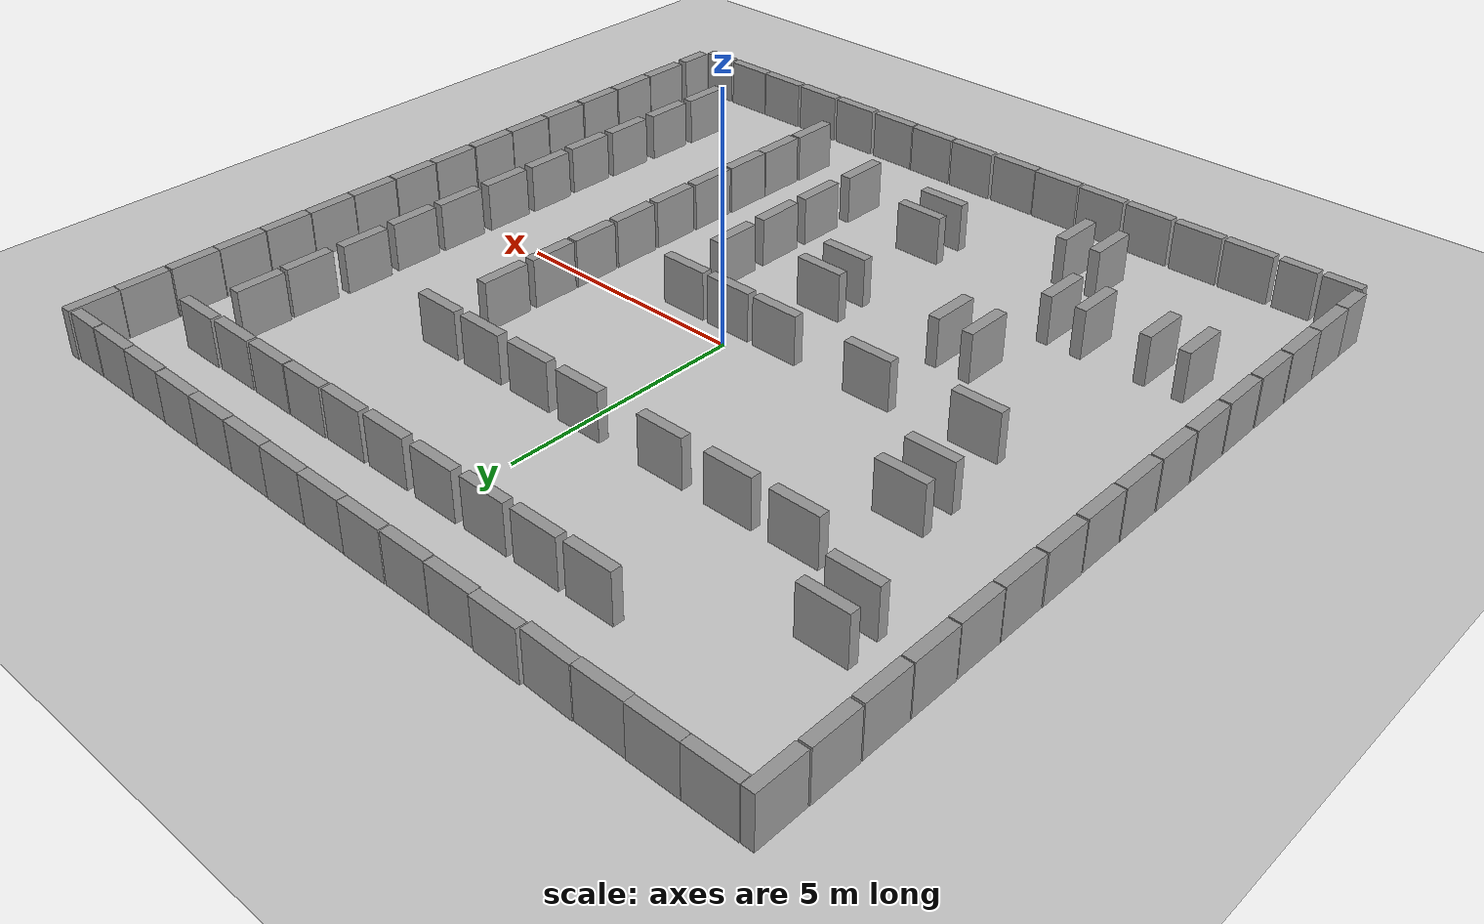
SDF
<sdf version="1.6">
 <world name="default">
  <light name="sun" type="directional">
   <pose>0 0 10 0 -0 0</pose>
   <diffuse>0.8 0.8 0.8 1</diffuse>
   <specular>0.1 0.1 0.1 1</specular>
   <attenuation>
    <range>1000</range>
    <constant>0.9</constant>
    <linear>0.01</linear>
    <quadratic>0.001</quadratic>
   </attenuation>
   <direction>-0.5 0.5 -1</direction>
  </light>
  <model name="ground_plane">
   <static>1</static>
   <static>1</static>
   <link name="link">
    <collision name="collision">
     <geometry><plane><normal>0 0 1</normal><size>100 100</size></plane></geometry>
     <surface><friction><ode><mu>100</mu><mu2>50</mu2></ode></friction></surface>
    </collision>
    <visual name="visual">
     <cast_shadows>0</cast_shadows>
     <geometry><plane><normal>0 0 1</normal><size>100 100</size></plane></geometry>
     <material>
      <script><uri>file://media/materials/scripts/gazebo.material</uri><name>Gazebo/Grey</name></script>
     </material>
    </visual>
   </link>
  </model>
  <gravity>0 0 -9.8</gravity>
  <magnetic_field>6e-06 2.3e-05 -4.2e-05</magnetic_field>
  <atmosphere type="adiabatic"/>
  <physics name="default_physics" default="0" type="ode">
   <max_step_size>0.001</max_step_size>
   <real_time_factor>1</real_time_factor>
   <real_time_update_rate>1000</real_time_update_rate>
  </physics>
  <scene><ambient>0.4 0.4 0.4 1</ambient><background>0.7 0.7 0.7 1</background><shadows>1</shadows></scene>
  <spherical_coordinates>
   <surface_model>EARTH_WGS84</surface_model>
   <latitude_deg>0</latitude_deg>
   <longitude_deg>0</longitude_deg>
   <elevation>0</elevation>
   <heading_deg>0</heading_deg>
  </spherical_coordinates>
  <audio><device>default</device></audio>
  <model name="unit_box_clone">
   <pose>-7.49845 8.12 0.5 0 -0 0.000368</pose>
   <link name="link">
    <inertial>
     <mass>1</mass>
     <inertia>
      <ixx>0.166667</ixx>
      <ixy>0</ixy>
      <ixz>0</ixz>
      <iyy>0.166667</iyy>
      <iyz>0</iyz>
      <izz>0.166667</izz>
     </inertia>
    </inertial>
    <collision name="collision"><geometry><box><size>1 0.210541 1</size></box></geometry></collision>
    <visual name="visual">
     <geometry><box><size>1 0.210541 1</size></box></geometry>
     <material>
      <script><name>Gazebo/Grey</name><uri>file://media/materials/scripts/gazebo.material</uri></script>
     </material>
    </visual>
   </link>
  </model>
  <model name="unit_box_clone_0">
   <pose>-6.49722 8.11979 0.5 0 -0 -0.00265</pose>
   <link name="link">
    <inertial>
     <mass>1</mass>
     <inertia>
      <ixx>0.166667</ixx>
      <ixy>0</ixy>
      <ixz>0</ixz>
      <iyy>0.166667</iyy>
      <iyz>0</iyz>
      <izz>0.166667</izz>
     </inertia>
    </inertial>
    <collision name="collision"><geometry><box><size>1 0.210541 1</size></box></geometry></collision>
    <visual name="visual">
     <geometry><box><size>1 0.210541 1</size></box></geometry>
     <material>
      <script><name>Gazebo/Grey</name><uri>file://media/materials/scripts/gazebo.material</uri></script>
     </material>
    </visual>
   </link>
  </model>
  <model name="unit_box_clone_1">
   <pose>-5.49725 8.10831 0.5 0 -0 -0.00265</pose>
   <link name="link">
    <inertial>
     <mass>1</mass>
     <inertia>
      <ixx>0.166667</ixx>
      <ixy>0</ixy>
      <ixz>0</ixz>
      <iyy>0.166667</iyy>
      <iyz>0</iyz>
      <izz>0.166667</izz>
     </inertia>
    </inertial>
    <collision name="collision"><geometry><box><size>1 0.210541 1</size></box></geometry></collision>
    <visual name="visual">
     <geometry><box><size>1 0.210541 1</size></box></geometry>
     <material>
      <script><name>Gazebo/Grey</name><uri>file://media/materials/scripts/gazebo.material</uri></script>
     </material>
    </visual>
   </link>
  </model>
  <model name="unit_box_clone_2">
   <pose>-4.49476 8.11056 0.5 0 -0 -0.026966</pose>
   <link name="link">
    <inertial>
     <mass>1</mass>
     <inertia>
      <ixx>0.166667</ixx>
      <ixy>0</ixy>
      <ixz>0</ixz>
      <iyy>0.166667</iyy>
      <iyz>0</iyz>
      <izz>0.166667</izz>
     </inertia>
    </inertial>
    <collision name="collision"><geometry><box><size>1 0.210541 1</size></box></geometry></collision>
    <visual name="visual">
     <geometry><box><size>1 0.210541 1</size></box></geometry>
     <material>
      <script><name>Gazebo/Grey</name><uri>file://media/materials/scripts/gazebo.material</uri></script>
     </material>
    </visual>
   </link>
  </model>
  <model name="unit_box_clone_3">
   <pose>-3.46833 8.14907 0.5 0 0 -0.008185</pose>
   <link name="link">
    <inertial>
     <mass>1</mass>
     <inertia>
      <ixx>0.166667</ixx>
      <ixy>0</ixy>
      <ixz>0</ixz>
      <iyy>0.166667</iyy>
      <iyz>0</iyz>
      <izz>0.166667</izz>
     </inertia>
    </inertial>
    <collision name="collision"><geometry><box><size>1 0.210541 1</size></box></geometry></collision>
    <visual name="visual">
     <geometry><box><size>1 0.210541 1</size></box></geometry>
     <material>
      <script><name>Gazebo/Grey</name><uri>file://media/materials/scripts/gazebo.material</uri></script>
     </material>
    </visual>
   </link>
  </model>
  <model name="unit_box_clone_4">
   <pose>-2.46316 8.11869 0.5 0 -0 0.000368</pose>
   <link name="link">
    <inertial>
     <mass>1</mass>
     <inertia>
      <ixx>0.166667</ixx>
      <ixy>0</ixy>
      <ixz>0</ixz>
      <iyy>0.166667</iyy>
      <iyz>0</iyz>
      <izz>0.166667</izz>
     </inertia>
    </inertial>
    <collision name="collision"><geometry><box><size>1 0.210541 1</size></box></geometry></collision>
    <visual name="visual">
     <geometry><box><size>1 0.210541 1</size></box></geometry>
     <material>
      <script><name>Gazebo/Grey</name><uri>file://media/materials/scripts/gazebo.material</uri></script>
     </material>
    </visual>
   </link>
  </model>
  <model name="unit_box_clone_5">
   <pose>-1.44425 8.11203 0.5 0 -0 0.000368</pose>
   <link name="link">
    <inertial>
     <mass>1</mass>
     <inertia>
      <ixx>0.166667</ixx>
      <ixy>0</ixy>
      <ixz>0</ixz>
      <iyy>0.166667</iyy>
      <iyz>0</iyz>
      <izz>0.166667</izz>
     </inertia>
    </inertial>
    <collision name="collision"><geometry><box><size>1 0.210541 1</size></box></geometry></collision>
    <visual name="visual">
     <geometry><box><size>1 0.210541 1</size></box></geometry>
     <material>
      <script><name>Gazebo/Grey</name><uri>file://media/materials/scripts/gazebo.material</uri></script>
     </material>
    </visual>
   </link>
  </model>
  <model name="unit_box_clone_6">
   <pose>-0.418678 8.11869 0.5 0 -0 0.000368</pose>
   <link name="link">
    <inertial>
     <mass>1</mass>
     <inertia>
      <ixx>0.166667</ixx>
      <ixy>0</ixy>
      <ixz>0</ixz>
      <iyy>0.166667</iyy>
      <iyz>0</iyz>
      <izz>0.166667</izz>
     </inertia>
    </inertial>
    <collision name="collision"><geometry><box><size>1 0.210541 1</size></box></geometry></collision>
    <visual name="visual">
     <geometry><box><size>1 0.210541 1</size></box></geometry>
     <material>
      <script><name>Gazebo/Grey</name><uri>file://media/materials/scripts/gazebo.material</uri></script>
     </material>
    </visual>
   </link>
  </model>
  <model name="unit_box_clone_7">
   <pose>0.592841 8.11155 0.5 0 -0 0.000368</pose>
   <link name="link">
    <inertial>
     <mass>1</mass>
     <inertia>
      <ixx>0.166667</ixx>
      <ixy>0</ixy>
      <ixz>0</ixz>
      <iyy>0.166667</iyy>
      <iyz>0</iyz>
      <izz>0.166667</izz>
     </inertia>
    </inertial>
    <collision name="collision"><geometry><box><size>1 0.210541 1</size></box></geometry></collision>
    <visual name="visual">
     <geometry><box><size>1 0.210541 1</size></box></geometry>
     <material>
      <script><name>Gazebo/Grey</name><uri>file://media/materials/scripts/gazebo.material</uri></script>
     </material>
    </visual>
   </link>
  </model>
  <model name="unit_box_clone_8">
   <pose>1.60043 8.11006 0.5 0 -0 0.000368</pose>
   <link name="link">
    <inertial>
     <mass>1</mass>
     <inertia>
      <ixx>0.166667</ixx>
      <ixy>0</ixy>
      <ixz>0</ixz>
      <iyy>0.166667</iyy>
      <iyz>0</iyz>
      <izz>0.166667</izz>
     </inertia>
    </inertial>
    <collision name="collision"><geometry><box><size>1 0.210541 1</size></box></geometry></collision>
    <visual name="visual">
     <geometry><box><size>1 0.210541 1</size></box></geometry>
     <material>
      <script><name>Gazebo/Grey</name><uri>file://media/materials/scripts/gazebo.material</uri></script>
     </material>
    </visual>
   </link>
  </model>
  <model name="unit_box_clone_9">
   <pose>2.60987 8.10287 0.5 0 -0 0.000368</pose>
   <link name="link">
    <inertial>
     <mass>1</mass>
     <inertia>
      <ixx>0.166667</ixx>
      <ixy>0</ixy>
      <ixz>0</ixz>
      <iyy>0.166667</iyy>
      <iyz>0</iyz>
      <izz>0.166667</izz>
     </inertia>
    </inertial>
    <collision name="collision"><geometry><box><size>1 0.210541 1</size></box></geometry></collision>
    <visual name="visual">
     <geometry><box><size>1 0.210541 1</size></box></geometry>
     <material>
      <script><name>Gazebo/Grey</name><uri>file://media/materials/scripts/gazebo.material</uri></script>
     </material>
    </visual>
   </link>
  </model>
  <model name="unit_box_clone_10">
   <pose>3.62649 8.09929 0.5 0 -0 0.000368</pose>
   <link name="link">
    <inertial>
     <mass>1</mass>
     <inertia>
      <ixx>0.166667</ixx>
      <ixy>0</ixy>
      <ixz>0</ixz>
      <iyy>0.166667</iyy>
      <iyz>0</iyz>
      <izz>0.166667</izz>
     </inertia>
    </inertial>
    <collision name="collision"><geometry><box><size>1 0.210541 1</size></box></geometry></collision>
    <visual name="visual">
     <geometry><box><size>1 0.210541 1</size></box></geometry>
     <material>
      <script><name>Gazebo/Grey</name><uri>file://media/materials/scripts/gazebo.material</uri></script>
     </material>
    </visual>
   </link>
  </model>
  <model name="unit_box_clone_11">
   <pose>4.63309 8.09531 0.5 0 0 -0.002817</pose>
   <link name="link">
    <inertial>
     <mass>1</mass>
     <inertia>
      <ixx>0.166667</ixx>
      <ixy>0</ixy>
      <ixz>0</ixz>
      <iyy>0.166667</iyy>
      <iyz>0</iyz>
      <izz>0.166667</izz>
     </inertia>
    </inertial>
    <collision name="collision"><geometry><box><size>1 0.210541 1</size></box></geometry></collision>
    <visual name="visual">
     <geometry><box><size>1 0.210541 1</size></box></geometry>
     <material>
      <script><name>Gazebo/Grey</name><uri>file://media/materials/scripts/gazebo.material</uri></script>
     </material>
    </visual>
   </link>
  </model>
  <model name="unit_box_0_clone_0">
   <pose>8.11522 6.68459 0.5 1e-06 1e-06 -0.000267</pose>
   <link name="link">
    <inertial>
     <mass>1</mass>
     <inertia>
      <ixx>0.166667</ixx>
      <ixy>0</ixy>
      <ixz>0</ixz>
      <iyy>0.166667</iyy>
      <iyz>0</iyz>
      <izz>0.166667</izz>
     </inertia>
    </inertial>
    <collision name="collision"><geometry><box><size>0.230819 1 1</size></box></geometry></collision>
    <visual name="visual">
     <geometry><box><size>0.230819 1 1</size></box></geometry>
     <material>
      <script><name>Gazebo/Grey</name><uri>file://media/materials/scripts/gazebo.material</uri></script>
     </material>
    </visual>
   </link>
  </model>
  <model name="unit_box_0_clone_1">
   <pose>8.11915 5.6517 0.5 -1e-06 1e-06 0.000146</pose>
   <link name="link">
    <inertial>
     <mass>1</mass>
     <inertia>
      <ixx>0.166667</ixx>
      <ixy>0</ixy>
      <ixz>0</ixz>
      <iyy>0.166667</iyy>
      <iyz>0</iyz>
      <izz>0.166667</izz>
     </inertia>
    </inertial>
    <collision name="collision"><geometry><box><size>0.230819 1 1</size></box></geometry></collision>
    <visual name="visual">
     <geometry><box><size>0.230819 1 1</size></box></geometry>
     <material>
      <script><name>Gazebo/Grey</name><uri>file://media/materials/scripts/gazebo.material</uri></script>
     </material>
    </visual>
   </link>
  </model>
  <model name="unit_box_0_clone_2">
   <pose>8.11914 4.64016 0.5 -1e-06 1e-06 0.000162</pose>
   <link name="link">
    <inertial>
     <mass>1</mass>
     <inertia>
      <ixx>0.166667</ixx>
      <ixy>0</ixy>
      <ixz>0</ixz>
      <iyy>0.166667</iyy>
      <iyz>0</iyz>
      <izz>0.166667</izz>
     </inertia>
    </inertial>
    <collision name="collision"><geometry><box><size>0.230819 1 1</size></box></geometry></collision>
    <visual name="visual">
     <geometry><box><size>0.230819 1 1</size></box></geometry>
     <material>
      <script><name>Gazebo/Grey</name><uri>file://media/materials/scripts/gazebo.material</uri></script>
     </material>
    </visual>
   </link>
  </model>
  <model name="unit_box_0_clone_3">
   <pose>8.11914 3.62227 0.5 1e-06 1e-06 0.000127</pose>
   <link name="link">
    <inertial>
     <mass>1</mass>
     <inertia>
      <ixx>0.166667</ixx>
      <ixy>0</ixy>
      <ixz>0</ixz>
      <iyy>0.166667</iyy>
      <iyz>0</iyz>
      <izz>0.166667</izz>
     </inertia>
    </inertial>
    <collision name="collision"><geometry><box><size>0.230819 1 1</size></box></geometry></collision>
    <visual name="visual">
     <geometry><box><size>0.230819 1 1</size></box></geometry>
     <material>
      <script><name>Gazebo/Grey</name><uri>file://media/materials/scripts/gazebo.material</uri></script>
     </material>
    </visual>
   </link>
  </model>
  <model name="unit_box_0_clone_4">
   <pose>8.11332 2.61061 0.5 1e-06 1e-06 -0.001398</pose>
   <link name="link">
    <inertial>
     <mass>1</mass>
     <inertia>
      <ixx>0.166667</ixx>
      <ixy>0</ixy>
      <ixz>0</ixz>
      <iyy>0.166667</iyy>
      <iyz>0</iyz>
      <izz>0.166667</izz>
     </inertia>
    </inertial>
    <collision name="collision"><geometry><box><size>0.230819 1 1</size></box></geometry></collision>
    <visual name="visual">
     <geometry><box><size>0.230819 1 1</size></box></geometry>
     <material>
      <script><name>Gazebo/Grey</name><uri>file://media/materials/scripts/gazebo.material</uri></script>
     </material>
    </visual>
   </link>
  </model>
  <model name="unit_box_0_clone_5">
   <pose>8.11277 1.5992 0.5 1e-06 1e-06 0.000127</pose>
   <link name="link">
    <inertial>
     <mass>1</mass>
     <inertia>
      <ixx>0.166667</ixx>
      <ixy>0</ixy>
      <ixz>0</ixz>
      <iyy>0.166667</iyy>
      <iyz>0</iyz>
      <izz>0.166667</izz>
     </inertia>
    </inertial>
    <collision name="collision"><geometry><box><size>0.230819 1 1</size></box></geometry></collision>
    <visual name="visual">
     <geometry><box><size>0.230819 1 1</size></box></geometry>
     <material>
      <script><name>Gazebo/Grey</name><uri>file://media/materials/scripts/gazebo.material</uri></script>
     </material>
    </visual>
   </link>
  </model>
  <model name="unit_box_0_clone_6">
   <pose>8.11277 0.574934 0.5 1e-06 1e-06 0.000127</pose>
   <link name="link">
    <inertial>
     <mass>1</mass>
     <inertia>
      <ixx>0.166667</ixx>
      <ixy>0</ixy>
      <ixz>0</ixz>
      <iyy>0.166667</iyy>
      <iyz>0</iyz>
      <izz>0.166667</izz>
     </inertia>
    </inertial>
    <collision name="collision"><geometry><box><size>0.230819 1 1</size></box></geometry></collision>
    <visual name="visual">
     <geometry><box><size>0.230819 1 1</size></box></geometry>
     <material>
      <script><name>Gazebo/Grey</name><uri>file://media/materials/scripts/gazebo.material</uri></script>
     </material>
    </visual>
   </link>
  </model>
  <model name="unit_box_0_clone_7">
   <pose>8.11276 -0.449324 0.5 1e-06 1e-06 0.000127</pose>
   <link name="link">
    <inertial>
     <mass>1</mass>
     <inertia>
      <ixx>0.166667</ixx>
      <ixy>0</ixy>
      <ixz>0</ixz>
      <iyy>0.166667</iyy>
      <iyz>0</iyz>
      <izz>0.166667</izz>
     </inertia>
    </inertial>
    <collision name="collision"><geometry><box><size>0.230819 1 1</size></box></geometry></collision>
    <visual name="visual">
     <geometry><box><size>0.230819 1 1</size></box></geometry>
     <material>
      <script><name>Gazebo/Grey</name><uri>file://media/materials/scripts/gazebo.material</uri></script>
     </material>
    </visual>
   </link>
  </model>
  <model name="unit_box_0_clone_8">
   <pose>8.11912 -1.4863 0.5 1e-06 1e-06 0.000127</pose>
   <link name="link">
    <inertial>
     <mass>1</mass>
     <inertia>
      <ixx>0.166667</ixx>
      <ixy>0</ixy>
      <ixz>0</ixz>
      <iyy>0.166667</iyy>
      <iyz>0</iyz>
      <izz>0.166667</izz>
     </inertia>
    </inertial>
    <collision name="collision"><geometry><box><size>0.230819 1 1</size></box></geometry></collision>
    <visual name="visual">
     <geometry><box><size>0.230819 1 1</size></box></geometry>
     <material>
      <script><name>Gazebo/Grey</name><uri>file://media/materials/scripts/gazebo.material</uri></script>
     </material>
    </visual>
   </link>
  </model>
  <model name="unit_box_0_clone_9">
   <pose>8.12548 -2.5042 0.5 1e-06 1e-06 0.000127</pose>
   <link name="link">
    <inertial>
     <mass>1</mass>
     <inertia>
      <ixx>0.166667</ixx>
      <ixy>0</ixy>
      <ixz>0</ixz>
      <iyy>0.166667</iyy>
      <iyz>0</iyz>
      <izz>0.166667</izz>
     </inertia>
    </inertial>
    <collision name="collision"><geometry><box><size>0.230819 1 1</size></box></geometry></collision>
    <visual name="visual">
     <geometry><box><size>0.230819 1 1</size></box></geometry>
     <material>
      <script><name>Gazebo/Grey</name><uri>file://media/materials/scripts/gazebo.material</uri></script>
     </material>
    </visual>
   </link>
  </model>
  <model name="unit_box_0_clone_10">
   <pose>8.12331 -3.52222 0.5 1e-06 1e-06 0.000127</pose>
   <link name="link">
    <inertial>
     <mass>1</mass>
     <inertia>
      <ixx>0.166667</ixx>
      <ixy>0</ixy>
      <ixz>0</ixz>
      <iyy>0.166667</iyy>
      <iyz>0</iyz>
      <izz>0.166667</izz>
     </inertia>
    </inertial>
    <collision name="collision"><geometry><box><size>0.230819 1 1</size></box></geometry></collision>
    <visual name="visual">
     <geometry><box><size>0.230819 1 1</size></box></geometry>
     <material>
      <script><name>Gazebo/Grey</name><uri>file://media/materials/scripts/gazebo.material</uri></script>
     </material>
    </visual>
   </link>
  </model>
  <model name="unit_box_0_clone_11">
   <pose>8.1233 -4.56315 0.5 1e-06 1e-06 0.000127</pose>
   <link name="link">
    <inertial>
     <mass>1</mass>
     <inertia>
      <ixx>0.166667</ixx>
      <ixy>0</ixy>
      <ixz>0</ixz>
      <iyy>0.166667</iyy>
      <iyz>0</iyz>
      <izz>0.166667</izz>
     </inertia>
    </inertial>
    <collision name="collision"><geometry><box><size>0.230819 1 1</size></box></geometry></collision>
    <visual name="visual">
     <geometry><box><size>0.230819 1 1</size></box></geometry>
     <material>
      <script><name>Gazebo/Grey</name><uri>file://media/materials/scripts/gazebo.material</uri></script>
     </material>
    </visual>
   </link>
  </model>
  <model name="unit_box_0_clone_12">
   <pose>8.11815 -5.59377 0.5 1e-06 1e-06 0.000127</pose>
   <link name="link">
    <inertial>
     <mass>1</mass>
     <inertia>
      <ixx>0.166667</ixx>
      <ixy>0</ixy>
      <ixz>0</ixz>
      <iyy>0.166667</iyy>
      <iyz>0</iyz>
      <izz>0.166667</izz>
     </inertia>
    </inertial>
    <collision name="collision"><geometry><box><size>0.230819 1 1</size></box></geometry></collision>
    <visual name="visual">
     <geometry><box><size>0.230819 1 1</size></box></geometry>
     <material>
      <script><name>Gazebo/Grey</name><uri>file://media/materials/scripts/gazebo.material</uri></script>
     </material>
    </visual>
   </link>
  </model>
  <model name="unit_box_0_clone_13">
   <pose>8.11333 -6.60776 0.5 1e-06 1e-06 -0.00535</pose>
   <link name="link">
    <inertial>
     <mass>1</mass>
     <inertia>
      <ixx>0.166667</ixx>
      <ixy>0</ixy>
      <ixz>0</ixz>
      <iyy>0.166667</iyy>
      <iyz>0</iyz>
      <izz>0.166667</izz>
     </inertia>
    </inertial>
    <collision name="collision"><geometry><box><size>0.230819 1 1</size></box></geometry></collision>
    <visual name="visual">
     <geometry><box><size>0.230819 1 1</size></box></geometry>
     <material>
      <script><name>Gazebo/Grey</name><uri>file://media/materials/scripts/gazebo.material</uri></script>
     </material>
    </visual>
   </link>
  </model>
  <model name="unit_box_clone_15_clone_0">
   <pose>6.71207 -8.13103 0.5 0 -0 0.000368</pose>
   <link name="link">
    <inertial>
     <mass>1</mass>
     <inertia>
      <ixx>0.166667</ixx>
      <ixy>0</ixy>
      <ixz>0</ixz>
      <iyy>0.166667</iyy>
      <iyz>0</iyz>
      <izz>0.166667</izz>
     </inertia>
    </inertial>
    <collision name="collision"><geometry><box><size>1 0.210541 1</size></box></geometry></collision>
    <visual name="visual">
     <geometry><box><size>1 0.210541 1</size></box></geometry>
     <material>
      <script><name>Gazebo/Grey</name><uri>file://media/materials/scripts/gazebo.material</uri></script>
     </material>
    </visual>
   </link>
  </model>
  <model name="unit_box_clone_15_clone_1">
   <pose>5.69715 -8.13103 0.5 0 -0 0.000368</pose>
   <link name="link">
    <inertial>
     <mass>1</mass>
     <inertia>
      <ixx>0.166667</ixx>
      <ixy>0</ixy>
      <ixz>0</ixz>
      <iyy>0.166667</iyy>
      <iyz>0</iyz>
      <izz>0.166667</izz>
     </inertia>
    </inertial>
    <collision name="collision"><geometry><box><size>1 0.210541 1</size></box></geometry></collision>
    <visual name="visual">
     <geometry><box><size>1 0.210541 1</size></box></geometry>
     <material>
      <script><name>Gazebo/Grey</name><uri>file://media/materials/scripts/gazebo.material</uri></script>
     </material>
    </visual>
   </link>
  </model>
  <model name="unit_box_clone_15_clone_2">
   <pose>4.63881 -8.13721 0.5 0 -0 0.000368</pose>
   <link name="link">
    <inertial>
     <mass>1</mass>
     <inertia>
      <ixx>0.166667</ixx>
      <ixy>0</ixy>
      <ixz>0</ixz>
      <iyy>0.166667</iyy>
      <iyz>0</iyz>
      <izz>0.166667</izz>
     </inertia>
    </inertial>
    <collision name="collision"><geometry><box><size>1 0.210541 1</size></box></geometry></collision>
    <visual name="visual">
     <geometry><box><size>1 0.210541 1</size></box></geometry>
     <material>
      <script><name>Gazebo/Grey</name><uri>file://media/materials/scripts/gazebo.material</uri></script>
     </material>
    </visual>
   </link>
  </model>
  <model name="unit_box_clone_15_clone_3">
   <pose>3.57975 -8.13721 0.5 0 -0 0.000368</pose>
   <link name="link">
    <inertial>
     <mass>1</mass>
     <inertia>
      <ixx>0.166667</ixx>
      <ixy>0</ixy>
      <ixz>0</ixz>
      <iyy>0.166667</iyy>
      <iyz>0</iyz>
      <izz>0.166667</izz>
     </inertia>
    </inertial>
    <collision name="collision"><geometry><box><size>1 0.210541 1</size></box></geometry></collision>
    <visual name="visual">
     <geometry><box><size>1 0.210541 1</size></box></geometry>
     <material>
      <script><name>Gazebo/Grey</name><uri>file://media/materials/scripts/gazebo.material</uri></script>
     </material>
    </visual>
   </link>
  </model>
  <model name="unit_box_clone_15_clone_4">
   <pose>2.49815 -8.13719 0.5 0 -0 0.000368</pose>
   <link name="link">
    <inertial>
     <mass>1</mass>
     <inertia>
      <ixx>0.166667</ixx>
      <ixy>0</ixy>
      <ixz>0</ixz>
      <iyy>0.166667</iyy>
      <iyz>0</iyz>
      <izz>0.166667</izz>
     </inertia>
    </inertial>
    <collision name="collision"><geometry><box><size>1 0.210541 1</size></box></geometry></collision>
    <visual name="visual">
     <geometry><box><size>1 0.210541 1</size></box></geometry>
     <material>
      <script><name>Gazebo/Grey</name><uri>file://media/materials/scripts/gazebo.material</uri></script>
     </material>
    </visual>
   </link>
  </model>
  <model name="unit_box_clone_15_clone_5">
   <pose>1.46162 -8.12592 0.5 0 -0 0.000368</pose>
   <link name="link">
    <inertial>
     <mass>1</mass>
     <inertia>
      <ixx>0.166667</ixx>
      <ixy>0</ixy>
      <ixz>0</ixz>
      <iyy>0.166667</iyy>
      <iyz>0</iyz>
      <izz>0.166667</izz>
     </inertia>
    </inertial>
    <collision name="collision"><geometry><box><size>1 0.210541 1</size></box></geometry></collision>
    <visual name="visual">
     <geometry><box><size>1 0.210541 1</size></box></geometry>
     <material>
      <script><name>Gazebo/Grey</name><uri>file://media/materials/scripts/gazebo.material</uri></script>
     </material>
    </visual>
   </link>
  </model>
  <model name="unit_box_clone_15_clone_6">
   <pose>0.425094 -8.12592 0.5 0 -0 0.000368</pose>
   <link name="link">
    <inertial>
     <mass>1</mass>
     <inertia>
      <ixx>0.166667</ixx>
      <ixy>0</ixy>
      <ixz>0</ixz>
      <iyy>0.166667</iyy>
      <iyz>0</iyz>
      <izz>0.166667</izz>
     </inertia>
    </inertial>
    <collision name="collision"><geometry><box><size>1 0.210541 1</size></box></geometry></collision>
    <visual name="visual">
     <geometry><box><size>1 0.210541 1</size></box></geometry>
     <material>
      <script><name>Gazebo/Grey</name><uri>file://media/materials/scripts/gazebo.material</uri></script>
     </material>
    </visual>
   </link>
  </model>
  <model name="unit_box_clone_15_clone_7">
   <pose>-0.633968 -8.14847 0.5 0 -0 0.000368</pose>
   <link name="link">
    <inertial>
     <mass>1</mass>
     <inertia>
      <ixx>0.166667</ixx>
      <ixy>0</ixy>
      <ixz>0</ixz>
      <iyy>0.166667</iyy>
      <iyz>0</iyz>
      <izz>0.166667</izz>
     </inertia>
    </inertial>
    <collision name="collision"><geometry><box><size>1 0.210541 1</size></box></geometry></collision>
    <visual name="visual">
     <geometry><box><size>1 0.210541 1</size></box></geometry>
     <material>
      <script><name>Gazebo/Grey</name><uri>file://media/materials/scripts/gazebo.material</uri></script>
     </material>
    </visual>
   </link>
  </model>
  <model name="unit_box_clone_15_clone_8">
   <pose>-1.65923 -8.13718 0.5 0 -0 0.000368</pose>
   <link name="link">
    <inertial>
     <mass>1</mass>
     <inertia>
      <ixx>0.166667</ixx>
      <ixy>0</ixy>
      <ixz>0</ixz>
      <iyy>0.166667</iyy>
      <iyz>0</iyz>
      <izz>0.166667</izz>
     </inertia>
    </inertial>
    <collision name="collision"><geometry><box><size>1 0.210541 1</size></box></geometry></collision>
    <visual name="visual">
     <geometry><box><size>1 0.210541 1</size></box></geometry>
     <material>
      <script><name>Gazebo/Grey</name><uri>file://media/materials/scripts/gazebo.material</uri></script>
     </material>
    </visual>
   </link>
  </model>
  <model name="unit_box_clone_15_clone_9">
   <pose>-2.70703 -8.12593 0.5 0 -0 0.000368</pose>
   <link name="link">
    <inertial>
     <mass>1</mass>
     <inertia>
      <ixx>0.166667</ixx>
      <ixy>0</ixy>
      <ixz>0</ixz>
      <iyy>0.166667</iyy>
      <iyz>0</iyz>
      <izz>0.166667</izz>
     </inertia>
    </inertial>
    <collision name="collision"><geometry><box><size>1 0.210541 1</size></box></geometry></collision>
    <visual name="visual">
     <geometry><box><size>1 0.210541 1</size></box></geometry>
     <material>
      <script><name>Gazebo/Grey</name><uri>file://media/materials/scripts/gazebo.material</uri></script>
     </material>
    </visual>
   </link>
  </model>
  <model name="unit_box_clone_15_clone_10">
   <pose>-3.77736 -8.12592 0.5 0 -0 0.000368</pose>
   <link name="link">
    <inertial>
     <mass>1</mass>
     <inertia>
      <ixx>0.166667</ixx>
      <ixy>0</ixy>
      <ixz>0</ixz>
      <iyy>0.166667</iyy>
      <iyz>0</iyz>
      <izz>0.166667</izz>
     </inertia>
    </inertial>
    <collision name="collision"><geometry><box><size>1 0.210541 1</size></box></geometry></collision>
    <visual name="visual">
     <geometry><box><size>1 0.210541 1</size></box></geometry>
     <material>
      <script><name>Gazebo/Grey</name><uri>file://media/materials/scripts/gazebo.material</uri></script>
     </material>
    </visual>
   </link>
  </model>
  <model name="unit_box_clone_15_clone_11">
   <pose>-4.85896 -8.11466 0.5 0 -0 0.000368</pose>
   <link name="link">
    <inertial>
     <mass>1</mass>
     <inertia>
      <ixx>0.166667</ixx>
      <ixy>0</ixy>
      <ixz>0</ixz>
      <iyy>0.166667</iyy>
      <iyz>0</iyz>
      <izz>0.166667</izz>
     </inertia>
    </inertial>
    <collision name="collision"><geometry><box><size>1 0.210541 1</size></box></geometry></collision>
    <visual name="visual">
     <geometry><box><size>1 0.210541 1</size></box></geometry>
     <material>
      <script><name>Gazebo/Grey</name><uri>file://media/materials/scripts/gazebo.material</uri></script>
     </material>
    </visual>
   </link>
  </model>
  <model name="unit_box_clone_15_clone_12">
   <pose>-5.91802 -8.11466 0.5 0 -0 0.000368</pose>
   <link name="link">
    <inertial>
     <mass>1</mass>
     <inertia>
      <ixx>0.166667</ixx>
      <ixy>0</ixy>
      <ixz>0</ixz>
      <iyy>0.166667</iyy>
      <iyz>0</iyz>
      <izz>0.166667</izz>
     </inertia>
    </inertial>
    <collision name="collision"><geometry><box><size>1 0.210541 1</size></box></geometry></collision>
    <visual name="visual">
     <geometry><box><size>1 0.210541 1</size></box></geometry>
     <material>
      <script><name>Gazebo/Grey</name><uri>file://media/materials/scripts/gazebo.material</uri></script>
     </material>
    </visual>
   </link>
  </model>
  <model name="unit_box_0_clone_4_clone">
   <pose>-8.12647 7.71769 0.5 1e-06 1e-06 0.000127</pose>
   <link name="link">
    <inertial>
     <mass>1</mass>
     <inertia>
      <ixx>0.166667</ixx>
      <ixy>0</ixy>
      <ixz>0</ixz>
      <iyy>0.166667</iyy>
      <iyz>0</iyz>
      <izz>0.166667</izz>
     </inertia>
    </inertial>
    <collision name="collision"><geometry><box><size>0.230819 1 1</size></box></geometry></collision>
    <visual name="visual">
     <geometry><box><size>0.230819 1 1</size></box></geometry>
     <material>
      <script><name>Gazebo/Grey</name><uri>file://media/materials/scripts/gazebo.material</uri></script>
     </material>
    </visual>
   </link>
  </model>
  <model name="unit_box_0_clone_4_clone_0">
   <pose>-8.13281 6.68715 0.5 1e-06 1e-06 0.000127</pose>
   <link name="link">
    <inertial>
     <mass>1</mass>
     <inertia>
      <ixx>0.166667</ixx>
      <ixy>0</ixy>
      <ixz>0</ixz>
      <iyy>0.166667</iyy>
      <iyz>0</iyz>
      <izz>0.166667</izz>
     </inertia>
    </inertial>
    <collision name="collision"><geometry><box><size>0.230819 1 1</size></box></geometry></collision>
    <visual name="visual">
     <geometry><box><size>0.230819 1 1</size></box></geometry>
     <material>
      <script><name>Gazebo/Grey</name><uri>file://media/materials/scripts/gazebo.material</uri></script>
     </material>
    </visual>
   </link>
  </model>
  <model name="unit_box_0_clone_4_clone_1">
   <pose>-8.12606 5.64723 0.5 1e-06 1e-06 0.000127</pose>
   <link name="link">
    <inertial>
     <mass>1</mass>
     <inertia>
      <ixx>0.166667</ixx>
      <ixy>0</ixy>
      <ixz>0</ixz>
      <iyy>0.166667</iyy>
      <iyz>0</iyz>
      <izz>0.166667</izz>
     </inertia>
    </inertial>
    <collision name="collision"><geometry><box><size>0.230819 1 1</size></box></geometry></collision>
    <visual name="visual">
     <geometry><box><size>0.230819 1 1</size></box></geometry>
     <material>
      <script><name>Gazebo/Grey</name><uri>file://media/materials/scripts/gazebo.material</uri></script>
     </material>
    </visual>
   </link>
  </model>
  <model name="unit_box_0_clone_4_clone_2">
   <pose>-8.12607 4.62081 0.5 1e-06 1e-06 0.000127</pose>
   <link name="link">
    <inertial>
     <mass>1</mass>
     <inertia>
      <ixx>0.166667</ixx>
      <ixy>0</ixy>
      <ixz>0</ixz>
      <iyy>0.166667</iyy>
      <iyz>0</iyz>
      <izz>0.166667</izz>
     </inertia>
    </inertial>
    <collision name="collision"><geometry><box><size>0.230819 1 1</size></box></geometry></collision>
    <visual name="visual">
     <geometry><box><size>0.230819 1 1</size></box></geometry>
     <material>
      <script><name>Gazebo/Grey</name><uri>file://media/materials/scripts/gazebo.material</uri></script>
     </material>
    </visual>
   </link>
  </model>
  <model name="unit_box_0_clone_4_clone_3">
   <pose>-8.11932 3.59439 0.5 1e-06 1e-06 0.000127</pose>
   <link name="link">
    <inertial>
     <mass>1</mass>
     <inertia>
      <ixx>0.166667</ixx>
      <ixy>0</ixy>
      <ixz>0</ixz>
      <iyy>0.166667</iyy>
      <iyz>0</iyz>
      <izz>0.166667</izz>
     </inertia>
    </inertial>
    <collision name="collision"><geometry><box><size>0.230819 1 1</size></box></geometry></collision>
    <visual name="visual">
     <geometry><box><size>0.230819 1 1</size></box></geometry>
     <material>
      <script><name>Gazebo/Grey</name><uri>file://media/materials/scripts/gazebo.material</uri></script>
     </material>
    </visual>
   </link>
  </model>
  <model name="unit_box_0_clone_4_clone_4">
   <pose>-8.11932 2.57473 0.5 1e-06 1e-06 0.000127</pose>
   <link name="link">
    <inertial>
     <mass>1</mass>
     <inertia>
      <ixx>0.166667</ixx>
      <ixy>0</ixy>
      <ixz>0</ixz>
      <iyy>0.166667</iyy>
      <iyz>0</iyz>
      <izz>0.166667</izz>
     </inertia>
    </inertial>
    <collision name="collision"><geometry><box><size>0.230819 1 1</size></box></geometry></collision>
    <visual name="visual">
     <geometry><box><size>0.230819 1 1</size></box></geometry>
     <material>
      <script><name>Gazebo/Grey</name><uri>file://media/materials/scripts/gazebo.material</uri></script>
     </material>
    </visual>
   </link>
  </model>
  <model name="unit_box_0_clone_4_clone_5">
   <pose>-8.12608 1.54156 0.5 1e-06 1e-06 0.000127</pose>
   <link name="link">
    <inertial>
     <mass>1</mass>
     <inertia>
      <ixx>0.166667</ixx>
      <ixy>0</ixy>
      <ixz>0</ixz>
      <iyy>0.166667</iyy>
      <iyz>0</iyz>
      <izz>0.166667</izz>
     </inertia>
    </inertial>
    <collision name="collision"><geometry><box><size>0.230819 1 1</size></box></geometry></collision>
    <visual name="visual">
     <geometry><box><size>0.230819 1 1</size></box></geometry>
     <material>
      <script><name>Gazebo/Grey</name><uri>file://media/materials/scripts/gazebo.material</uri></script>
     </material>
    </visual>
   </link>
  </model>
  <model name="unit_box_0_clone_4_clone_6">
   <pose>-8.11933 0.501626 0.5 1e-06 1e-06 0.000127</pose>
   <link name="link">
    <inertial>
     <mass>1</mass>
     <inertia>
      <ixx>0.166667</ixx>
      <ixy>0</ixy>
      <ixz>0</ixz>
      <iyy>0.166667</iyy>
      <iyz>0</iyz>
      <izz>0.166667</izz>
     </inertia>
    </inertial>
    <collision name="collision"><geometry><box><size>0.230819 1 1</size></box></geometry></collision>
    <visual name="visual">
     <geometry><box><size>0.230819 1 1</size></box></geometry>
     <material>
      <script><name>Gazebo/Grey</name><uri>file://media/materials/scripts/gazebo.material</uri></script>
     </material>
    </visual>
   </link>
  </model>
  <model name="unit_box_0_clone_4_clone_7">
   <pose>-8.12609 -0.518038 0.5 1e-06 1e-06 0.000127</pose>
   <link name="link">
    <inertial>
     <mass>1</mass>
     <inertia>
      <ixx>0.166667</ixx>
      <ixy>0</ixy>
      <ixz>0</ixz>
      <iyy>0.166667</iyy>
      <iyz>0</iyz>
      <izz>0.166667</izz>
     </inertia>
    </inertial>
    <collision name="collision"><geometry><box><size>0.230819 1 1</size></box></geometry></collision>
    <visual name="visual">
     <geometry><box><size>0.230819 1 1</size></box></geometry>
     <material>
      <script><name>Gazebo/Grey</name><uri>file://media/materials/scripts/gazebo.material</uri></script>
     </material>
    </visual>
   </link>
  </model>
  <model name="unit_box_0_clone_4_clone_8">
   <pose>-8.13284 -1.54445 0.5 1e-06 1e-06 0.000127</pose>
   <link name="link">
    <inertial>
     <mass>1</mass>
     <inertia>
      <ixx>0.166667</ixx>
      <ixy>0</ixy>
      <ixz>0</ixz>
      <iyy>0.166667</iyy>
      <iyz>0</iyz>
      <izz>0.166667</izz>
     </inertia>
    </inertial>
    <collision name="collision"><geometry><box><size>0.230819 1 1</size></box></geometry></collision>
    <visual name="visual">
     <geometry><box><size>0.230819 1 1</size></box></geometry>
     <material>
      <script><name>Gazebo/Grey</name><uri>file://media/materials/scripts/gazebo.material</uri></script>
     </material>
    </visual>
   </link>
  </model>
  <model name="unit_box_0_clone_4_clone_9">
   <pose>-8.13285 -2.58437 0.5 1e-06 1e-06 0.000127</pose>
   <link name="link">
    <inertial>
     <mass>1</mass>
     <inertia>
      <ixx>0.166667</ixx>
      <ixy>0</ixy>
      <ixz>0</ixz>
      <iyy>0.166667</iyy>
      <iyz>0</iyz>
      <izz>0.166667</izz>
     </inertia>
    </inertial>
    <collision name="collision"><geometry><box><size>0.230819 1 1</size></box></geometry></collision>
    <visual name="visual">
     <geometry><box><size>0.230819 1 1</size></box></geometry>
     <material>
      <script><name>Gazebo/Grey</name><uri>file://media/materials/scripts/gazebo.material</uri></script>
     </material>
    </visual>
   </link>
  </model>
  <model name="unit_box_0_clone_4_clone_10">
   <pose>-8.13285 -3.62429 0.5 1e-06 1e-06 0.000127</pose>
   <link name="link">
    <inertial>
     <mass>1</mass>
     <inertia>
      <ixx>0.166667</ixx>
      <ixy>0</ixy>
      <ixz>0</ixz>
      <iyy>0.166667</iyy>
      <iyz>0</iyz>
      <izz>0.166667</izz>
     </inertia>
    </inertial>
    <collision name="collision"><geometry><box><size>0.230819 1 1</size></box></geometry></collision>
    <visual name="visual">
     <geometry><box><size>0.230819 1 1</size></box></geometry>
     <material>
      <script><name>Gazebo/Grey</name><uri>file://media/materials/scripts/gazebo.material</uri></script>
     </material>
    </visual>
   </link>
  </model>
  <model name="unit_box_0_clone_4_clone_11">
   <pose>-8.1396 -4.65746 0.5 1e-06 1e-06 0.000127</pose>
   <link name="link">
    <inertial>
     <mass>1</mass>
     <inertia>
      <ixx>0.166667</ixx>
      <ixy>0</ixy>
      <ixz>0</ixz>
      <iyy>0.166667</iyy>
      <iyz>0</iyz>
      <izz>0.166667</izz>
     </inertia>
    </inertial>
    <collision name="collision"><geometry><box><size>0.230819 1 1</size></box></geometry></collision>
    <visual name="visual">
     <geometry><box><size>0.230819 1 1</size></box></geometry>
     <material>
      <script><name>Gazebo/Grey</name><uri>file://media/materials/scripts/gazebo.material</uri></script>
     </material>
    </visual>
   </link>
  </model>
  <model name="unit_box_0_clone_4_clone_12">
   <pose>-8.1396 -5.69063 0.5 1e-06 1e-06 0.000127</pose>
   <link name="link">
    <inertial>
     <mass>1</mass>
     <inertia>
      <ixx>0.166667</ixx>
      <ixy>0</ixy>
      <ixz>0</ixz>
      <iyy>0.166667</iyy>
      <iyz>0</iyz>
      <izz>0.166667</izz>
     </inertia>
    </inertial>
    <collision name="collision"><geometry><box><size>0.230819 1 1</size></box></geometry></collision>
    <visual name="visual">
     <geometry><box><size>0.230819 1 1</size></box></geometry>
     <material>
      <script><name>Gazebo/Grey</name><uri>file://media/materials/scripts/gazebo.material</uri></script>
     </material>
    </visual>
   </link>
  </model>
  <model name="unit_box_0_clone_4_clone_13">
   <pose>-8.14113 -6.70873 0.499998 4e-06 0 -0.008675</pose>
   <link name="link">
    <inertial>
     <mass>1</mass>
     <inertia>
      <ixx>0.166667</ixx>
      <ixy>0</ixy>
      <ixz>0</ixz>
      <iyy>0.166667</iyy>
      <iyz>0</iyz>
      <izz>0.166667</izz>
     </inertia>
    </inertial>
    <collision name="collision"><geometry><box><size>0.230819 1 1</size></box></geometry></collision>
    <visual name="visual">
     <geometry><box><size>0.230819 1 1</size></box></geometry>
     <material>
      <script><name>Gazebo/Grey</name><uri>file://media/materials/scripts/gazebo.material</uri></script>
     </material>
    </visual>
   </link>
  </model>
  <model name="unit_box_0_clone_0_clone">
   <pose>8.11438 7.69322 0.5 -1e-06 1e-06 0.000128</pose>
   <link name="link">
    <inertial>
     <mass>1</mass>
     <inertia>
      <ixx>0.166667</ixx>
      <ixy>0</ixy>
      <ixz>0</ixz>
      <iyy>0.166667</iyy>
      <iyz>0</iyz>
      <izz>0.166667</izz>
     </inertia>
    </inertial>
    <collision name="collision"><geometry><box><size>0.230819 1 1</size></box></geometry></collision>
    <visual name="visual">
     <geometry><box><size>0.230819 1 1</size></box></geometry>
     <material>
      <script><name>Gazebo/Grey</name><uri>file://media/materials/scripts/gazebo.material</uri></script>
     </material>
    </visual>
   </link>
  </model>
  <model name="unit_box_clone_11_clone">
   <pose>5.65439 8.08315 0.5 0 0 -0.00319</pose>
   <link name="link">
    <inertial>
     <mass>1</mass>
     <inertia>
      <ixx>0.166667</ixx>
      <ixy>0</ixy>
      <ixz>0</ixz>
      <iyy>0.166667</iyy>
      <iyz>0</iyz>
      <izz>0.166667</izz>
     </inertia>
    </inertial>
    <collision name="collision"><geometry><box><size>1 0.210541 1</size></box></geometry></collision>
    <visual name="visual">
     <geometry><box><size>1 0.210541 1</size></box></geometry>
     <material>
      <script><name>Gazebo/Grey</name><uri>file://media/materials/scripts/gazebo.material</uri></script>
     </material>
    </visual>
   </link>
  </model>
  <model name="unit_box_clone_11_clone_0">
   <pose>6.6644 8.0733 0.5 -0 -0 -0.003093</pose>
   <link name="link">
    <inertial>
     <mass>1</mass>
     <inertia>
      <ixx>0.166667</ixx>
      <ixy>0</ixy>
      <ixz>0</ixz>
      <iyy>0.166667</iyy>
      <iyz>0</iyz>
      <izz>0.166667</izz>
     </inertia>
    </inertial>
    <collision name="collision"><geometry><box><size>1 0.210541 1</size></box></geometry></collision>
    <visual name="visual">
     <geometry><box><size>1 0.210541 1</size></box></geometry>
     <material>
      <script><name>Gazebo/Grey</name><uri>file://media/materials/scripts/gazebo.material</uri></script>
     </material>
    </visual>
   </link>
  </model>
  <model name="unit_box_clone_11_clone_1_clone">
   <pose>7.56437 8.07322 0.499997 2e-06 -8e-06 0.001439</pose>
   <link name="link">
    <inertial>
     <mass>1</mass>
     <inertia>
      <ixx>0.166667</ixx>
      <ixy>0</ixy>
      <ixz>0</ixz>
      <iyy>0.166667</iyy>
      <iyz>0</iyz>
      <izz>0.166667</izz>
     </inertia>
    </inertial>
    <collision name="collision"><geometry><box><size>0.750223 0.210541 1</size></box></geometry></collision>
    <visual name="visual">
     <geometry><box><size>0.750223 0.210541 1</size></box></geometry>
     <material>
      <script><name>Gazebo/Grey</name><uri>file://media/materials/scripts/gazebo.material</uri></script>
     </material>
    </visual>
   </link>
  </model>
  <model name="unit_box_clone_11_clone_1_clone_0">
   <pose>-6.9088 -8.11956 0.499997 -2e-06 8e-06 -0.007145</pose>
   <link name="link">
    <inertial>
     <mass>1</mass>
     <inertia>
      <ixx>0.166667</ixx>
      <ixy>0</ixy>
      <ixz>0</ixz>
      <iyy>0.166667</iyy>
      <iyz>0</iyz>
      <izz>0.166667</izz>
     </inertia>
    </inertial>
    <collision name="collision"><geometry><box><size>0.750223 0.210541 1</size></box></geometry></collision>
    <visual name="visual">
     <geometry><box><size>0.750223 0.210541 1</size></box></geometry>
     <material>
      <script><name>Gazebo/Grey</name><uri>file://media/materials/scripts/gazebo.material</uri></script>
     </material>
    </visual>
   </link>
  </model>
  <model name="unit_box_0_clone_4_clone_13_clone_clone">
   <pose>-8.13833 -7.5766 0.499998 -6e-06 2e-06 -0.013533</pose>
   <link name="link">
    <inertial>
     <mass>1</mass>
     <inertia>
      <ixx>0.166667</ixx>
      <ixy>0</ixy>
      <ixz>0</ixz>
      <iyy>0.166667</iyy>
      <iyz>0</iyz>
      <izz>0.166667</izz>
     </inertia>
    </inertial>
    <collision name="collision"><geometry><box><size>0.230819 0.700336 1</size></box></geometry></collision>
    <visual name="visual">
     <geometry><box><size>0.230819 0.700336 1</size></box></geometry>
     <material>
      <script><name>Gazebo/Grey</name><uri>file://media/materials/scripts/gazebo.material</uri></script>
     </material>
    </visual>
   </link>
  </model>
  <model name="unit_box_clone_11_clone_1_clone_0_clone">
   <pose>-7.75476 -8.122 0.5 0 1e-06 -0.001913</pose>
   <link name="link">
    <inertial>
     <mass>1</mass>
     <inertia>
      <ixx>0.166667</ixx>
      <ixy>0</ixy>
      <ixz>0</ixz>
      <iyy>0.166667</iyy>
      <iyz>0</iyz>
      <izz>0.166667</izz>
     </inertia>
    </inertial>
    <collision name="collision"><geometry><box><size>0.750223 0.210541 1</size></box></geometry></collision>
    <visual name="visual">
     <geometry><box><size>0.750223 0.210541 1</size></box></geometry>
     <material>
      <script><name>Gazebo/Grey</name><uri>file://media/materials/scripts/gazebo.material</uri></script>
     </material>
    </visual>
   </link>
  </model>
  <model name="unit_box_clone_11_clone_1_clone_2">
   <pose>7.6425 -8.13929 0.500001 0 -1e-06 0.003846</pose>
   <link name="link">
    <inertial>
     <mass>1</mass>
     <inertia>
      <ixx>0.166667</ixx>
      <ixy>0</ixy>
      <ixz>0</ixz>
      <iyy>0.166667</iyy>
      <iyz>0</iyz>
      <izz>0.166667</izz>
     </inertia>
    </inertial>
    <collision name="collision"><geometry><box><size>0.750223 0.210541 1</size></box></geometry></collision>
    <visual name="visual">
     <geometry><box><size>0.750223 0.210541 1</size></box></geometry>
     <material>
      <script><name>Gazebo/Grey</name><uri>file://media/materials/scripts/gazebo.material</uri></script>
     </material>
    </visual>
   </link>
  </model>
  <model name="unit_box_0_clone_4_clone_13_clone_clone_clone">
   <pose>8.11858 -7.62155 0.499997 7e-06 3e-06 -0.007198</pose>
   <link name="link">
    <inertial>
     <mass>1</mass>
     <inertia>
      <ixx>0.166667</ixx>
      <ixy>0</ixy>
      <ixz>0</ixz>
      <iyy>0.166667</iyy>
      <iyz>0</iyz>
      <izz>0.166667</izz>
     </inertia>
    </inertial>
    <collision name="collision"><geometry><box><size>0.230819 0.700336 1</size></box></geometry></collision>
    <visual name="visual">
     <geometry><box><size>0.230819 0.700336 1</size></box></geometry>
     <material>
      <script><name>Gazebo/Grey</name><uri>file://media/materials/scripts/gazebo.material</uri></script>
     </material>
    </visual>
   </link>
  </model>
  <model name="unit_box_clone_11_clone_clone">
   <pose>6.45565 6.53019 0.5 -0 -0 -0.003103</pose>
   <link name="link">
    <inertial>
     <mass>1</mass>
     <inertia>
      <ixx>0.166667</ixx>
      <ixy>0</ixy>
      <ixz>0</ixz>
      <iyy>0.166667</iyy>
      <iyz>0</iyz>
      <izz>0.166667</izz>
     </inertia>
    </inertial>
    <collision name="collision"><geometry><box><size>1 0.210541 1</size></box></geometry></collision>
    <visual name="visual">
     <geometry><box><size>1 0.210541 1</size></box></geometry>
     <material>
      <script><name>Gazebo/Grey</name><uri>file://media/materials/scripts/gazebo.material</uri></script>
     </material>
    </visual>
   </link>
  </model>
  <model name="unit_box_clone_11_clone_clone_0">
   <pose>5.38299 6.51467 0.5 0 0 -0.003162</pose>
   <link name="link">
    <inertial>
     <mass>1</mass>
     <inertia>
      <ixx>0.166667</ixx>
      <ixy>0</ixy>
      <ixz>0</ixz>
      <iyy>0.166667</iyy>
      <iyz>0</iyz>
      <izz>0.166667</izz>
     </inertia>
    </inertial>
    <collision name="collision"><geometry><box><size>1 0.210541 1</size></box></geometry></collision>
    <visual name="visual">
     <geometry><box><size>1 0.210541 1</size></box></geometry>
     <material>
      <script><name>Gazebo/Grey</name><uri>file://media/materials/scripts/gazebo.material</uri></script>
     </material>
    </visual>
   </link>
  </model>
  <model name="unit_box_clone_11_clone_clone_1">
   <pose>4.32587 6.51468 0.5 -0 -0 -0.003062</pose>
   <link name="link">
    <inertial>
     <mass>1</mass>
     <inertia>
      <ixx>0.166667</ixx>
      <ixy>0</ixy>
      <ixz>0</ixz>
      <iyy>0.166667</iyy>
      <iyz>0</iyz>
      <izz>0.166667</izz>
     </inertia>
    </inertial>
    <collision name="collision"><geometry><box><size>1 0.210541 1</size></box></geometry></collision>
    <visual name="visual">
     <geometry><box><size>1 0.210541 1</size></box></geometry>
     <material>
      <script><name>Gazebo/Grey</name><uri>file://media/materials/scripts/gazebo.material</uri></script>
     </material>
    </visual>
   </link>
  </model>
  <model name="unit_box_clone_11_clone_clone_2">
   <pose>3.29984 6.51466 0.5 -0 -0 -0.003236</pose>
   <link name="link">
    <inertial>
     <mass>1</mass>
     <inertia>
      <ixx>0.166667</ixx>
      <ixy>0</ixy>
      <ixz>0</ixz>
      <iyy>0.166667</iyy>
      <iyz>0</iyz>
      <izz>0.166667</izz>
     </inertia>
    </inertial>
    <collision name="collision"><geometry><box><size>1 0.210541 1</size></box></geometry></collision>
    <visual name="visual">
     <geometry><box><size>1 0.210541 1</size></box></geometry>
     <material>
      <script><name>Gazebo/Grey</name><uri>file://media/materials/scripts/gazebo.material</uri></script>
     </material>
    </visual>
   </link>
  </model>
  <model name="unit_box_clone_11_clone_clone_3">
   <pose>2.25828 6.4991 0.5 0 0 -0.003047</pose>
   <link name="link">
    <inertial>
     <mass>1</mass>
     <inertia>
      <ixx>0.166667</ixx>
      <ixy>0</ixy>
      <ixz>0</ixz>
      <iyy>0.166667</iyy>
      <iyz>0</iyz>
      <izz>0.166667</izz>
     </inertia>
    </inertial>
    <collision name="collision"><geometry><box><size>1 0.210541 1</size></box></geometry></collision>
    <visual name="visual">
     <geometry><box><size>1 0.210541 1</size></box></geometry>
     <material>
      <script><name>Gazebo/Grey</name><uri>file://media/materials/scripts/gazebo.material</uri></script>
     </material>
    </visual>
   </link>
  </model>
  <model name="unit_box_clone_11_clone_clone_4">
   <pose>1.15453 6.48355 0.5 0 0 -0.003067</pose>
   <link name="link">
    <inertial>
     <mass>1</mass>
     <inertia>
      <ixx>0.166667</ixx>
      <ixy>0</ixy>
      <ixz>0</ixz>
      <iyy>0.166667</iyy>
      <iyz>0</iyz>
      <izz>0.166667</izz>
     </inertia>
    </inertial>
    <collision name="collision"><geometry><box><size>1 0.210541 1</size></box></geometry></collision>
    <visual name="visual">
     <geometry><box><size>1 0.210541 1</size></box></geometry>
     <material>
      <script><name>Gazebo/Grey</name><uri>file://media/materials/scripts/gazebo.material</uri></script>
     </material>
    </visual>
   </link>
  </model>
  <model name="unit_box_clone_11_clone_clone_5">
   <pose>-0.058049 6.49917 0.5 0 -0 -0.003116</pose>
   <link name="link">
    <inertial>
     <mass>1</mass>
     <inertia>
      <ixx>0.166667</ixx>
      <ixy>0</ixy>
      <ixz>0</ixz>
      <iyy>0.166667</iyy>
      <iyz>0</iyz>
      <izz>0.166667</izz>
     </inertia>
    </inertial>
    <collision name="collision"><geometry><box><size>1 0.210541 1</size></box></geometry></collision>
    <visual name="visual">
     <geometry><box><size>1 0.210541 1</size></box></geometry>
     <material>
      <script><name>Gazebo/Grey</name><uri>file://media/materials/scripts/gazebo.material</uri></script>
     </material>
    </visual>
   </link>
  </model>
  <model name="unit_box_clone_11_clone_clone_6">
   <pose>-1.23953 6.48361 0.5 0 0 -0.003163</pose>
   <link name="link">
    <inertial>
     <mass>1</mass>
     <inertia>
      <ixx>0.166667</ixx>
      <ixy>0</ixy>
      <ixz>0</ixz>
      <iyy>0.166667</iyy>
      <iyz>0</iyz>
      <izz>0.166667</izz>
     </inertia>
    </inertial>
    <collision name="collision"><geometry><box><size>1 0.210541 1</size></box></geometry></collision>
    <visual name="visual">
     <geometry><box><size>1 0.210541 1</size></box></geometry>
     <material>
      <script><name>Gazebo/Grey</name><uri>file://media/materials/scripts/gazebo.material</uri></script>
     </material>
    </visual>
   </link>
  </model>
  <model name="unit_box_clone_11_clone_clone_7">
   <pose>-2.40547 6.48363 0.5 -0 -0 -0.003058</pose>
   <link name="link">
    <inertial>
     <mass>1</mass>
     <inertia>
      <ixx>0.166667</ixx>
      <ixy>0</ixy>
      <ixz>0</ixz>
      <iyy>0.166667</iyy>
      <iyz>0</iyz>
      <izz>0.166667</izz>
     </inertia>
    </inertial>
    <collision name="collision"><geometry><box><size>1 0.210541 1</size></box></geometry></collision>
    <visual name="visual">
     <geometry><box><size>1 0.210541 1</size></box></geometry>
     <material>
      <script><name>Gazebo/Grey</name><uri>file://media/materials/scripts/gazebo.material</uri></script>
     </material>
    </visual>
   </link>
  </model>
  <model name="unit_box_clone_11_clone_clone_8">
   <pose>-3.54032 6.46807 0.5 -0 -0 -0.003114</pose>
   <link name="link">
    <inertial>
     <mass>1</mass>
     <inertia>
      <ixx>0.166667</ixx>
      <ixy>0</ixy>
      <ixz>0</ixz>
      <iyy>0.166667</iyy>
      <iyz>0</iyz>
      <izz>0.166667</izz>
     </inertia>
    </inertial>
    <collision name="collision"><geometry><box><size>1 0.210541 1</size></box></geometry></collision>
    <visual name="visual">
     <geometry><box><size>1 0.210541 1</size></box></geometry>
     <material>
      <script><name>Gazebo/Grey</name><uri>file://media/materials/scripts/gazebo.material</uri></script>
     </material>
    </visual>
   </link>
  </model>
  <model name="unit_box_0_clone_13_clone">
   <pose>6.53015 5.30329 0.499998 -4e-06 -0 -0.005553</pose>
   <link name="link">
    <inertial>
     <mass>1</mass>
     <inertia>
      <ixx>0.166667</ixx>
      <ixy>0</ixy>
      <ixz>0</ixz>
      <iyy>0.166667</iyy>
      <iyz>0</iyz>
      <izz>0.166667</izz>
     </inertia>
    </inertial>
    <collision name="collision"><geometry><box><size>0.230819 1 1</size></box></geometry></collision>
    <visual name="visual">
     <geometry><box><size>0.230819 1 1</size></box></geometry>
     <material>
      <script><name>Gazebo/Grey</name><uri>file://media/materials/scripts/gazebo.material</uri></script>
     </material>
    </visual>
   </link>
  </model>
  <model name="unit_box_0_clone_13_clone_0">
   <pose>6.55676 4.22554 0.499998 -4e-06 0 -0.005523</pose>
   <link name="link">
    <inertial>
     <mass>1</mass>
     <inertia>
      <ixx>0.166667</ixx>
      <ixy>0</ixy>
      <ixz>0</ixz>
      <iyy>0.166667</iyy>
      <iyz>0</iyz>
      <izz>0.166667</izz>
     </inertia>
    </inertial>
    <collision name="collision"><geometry><box><size>0.230819 1 1</size></box></geometry></collision>
    <visual name="visual">
     <geometry><box><size>0.230819 1 1</size></box></geometry>
     <material>
      <script><name>Gazebo/Grey</name><uri>file://media/materials/scripts/gazebo.material</uri></script>
     </material>
    </visual>
   </link>
  </model>
  <model name="unit_box_0_clone_13_clone_1">
   <pose>6.53014 3 0.5 1e-06 -1e-06 -0.005523</pose>
   <link name="link">
    <inertial>
     <mass>1</mass>
     <inertia>
      <ixx>0.166667</ixx>
      <ixy>0</ixy>
      <ixz>0</ixz>
      <iyy>0.166667</iyy>
      <iyz>0</iyz>
      <izz>0.166667</izz>
     </inertia>
    </inertial>
    <collision name="collision"><geometry><box><size>0.230819 1 1</size></box></geometry></collision>
    <visual name="visual">
     <geometry><box><size>0.230819 1 1</size></box></geometry>
     <material>
      <script><name>Gazebo/Grey</name><uri>file://media/materials/scripts/gazebo.material</uri></script>
     </material>
    </visual>
   </link>
  </model>
  <model name="unit_box_0_clone_13_clone_2">
   <pose>6.55675 1.81724 0.5 1e-06 -1e-06 -0.00555</pose>
   <link name="link">
    <inertial>
     <mass>1</mass>
     <inertia>
      <ixx>0.166667</ixx>
      <ixy>0</ixy>
      <ixz>0</ixz>
      <iyy>0.166667</iyy>
      <iyz>0</iyz>
      <izz>0.166667</izz>
     </inertia>
    </inertial>
    <collision name="collision"><geometry><box><size>0.230819 1 1</size></box></geometry></collision>
    <visual name="visual">
     <geometry><box><size>0.230819 1 1</size></box></geometry>
     <material>
      <script><name>Gazebo/Grey</name><uri>file://media/materials/scripts/gazebo.material</uri></script>
     </material>
    </visual>
   </link>
  </model>
  <model name="unit_box_0_clone_13_clone_3">
   <pose>6.54343 0.686271 0.5 1e-06 1e-06 -0.005373</pose>
   <link name="link">
    <inertial>
     <mass>1</mass>
     <inertia>
      <ixx>0.166667</ixx>
      <ixy>0</ixy>
      <ixz>0</ixz>
      <iyy>0.166667</iyy>
      <iyz>0</iyz>
      <izz>0.166667</izz>
     </inertia>
    </inertial>
    <collision name="collision"><geometry><box><size>0.230819 1 1</size></box></geometry></collision>
    <visual name="visual">
     <geometry><box><size>0.230819 1 1</size></box></geometry>
     <material>
      <script><name>Gazebo/Grey</name><uri>file://media/materials/scripts/gazebo.material</uri></script>
     </material>
    </visual>
   </link>
  </model>
  <model name="unit_box_0_clone_13_clone_4">
   <pose>6.53012 -0.497923 0.499998 4e-06 -0 -0.005253</pose>
   <link name="link">
    <inertial>
     <mass>1</mass>
     <inertia>
      <ixx>0.166667</ixx>
      <ixy>0</ixy>
      <ixz>0</ixz>
      <iyy>0.166667</iyy>
      <iyz>0</iyz>
      <izz>0.166667</izz>
     </inertia>
    </inertial>
    <collision name="collision"><geometry><box><size>0.230819 1 1</size></box></geometry></collision>
    <visual name="visual">
     <geometry><box><size>0.230819 1 1</size></box></geometry>
     <material>
      <script><name>Gazebo/Grey</name><uri>file://media/materials/scripts/gazebo.material</uri></script>
     </material>
    </visual>
   </link>
  </model>
  <model name="unit_box_0_clone_13_clone_5">
   <pose>6.51681 -1.6422 0.499998 -4e-06 0 -0.005533</pose>
   <link name="link">
    <inertial>
     <mass>1</mass>
     <inertia>
      <ixx>0.166667</ixx>
      <ixy>0</ixy>
      <ixz>0</ixz>
      <iyy>0.166667</iyy>
      <iyz>0</iyz>
      <izz>0.166667</izz>
     </inertia>
    </inertial>
    <collision name="collision"><geometry><box><size>0.230819 1 1</size></box></geometry></collision>
    <visual name="visual">
     <geometry><box><size>0.230819 1 1</size></box></geometry>
     <material>
      <script><name>Gazebo/Grey</name><uri>file://media/materials/scripts/gazebo.material</uri></script>
     </material>
    </visual>
   </link>
  </model>
  <model name="unit_box_0_clone_13_clone_6">
   <pose>6.55672 -2.78647 0.499998 4e-06 -0 -0.005215</pose>
   <link name="link">
    <inertial>
     <mass>1</mass>
     <inertia>
      <ixx>0.166667</ixx>
      <ixy>0</ixy>
      <ixz>0</ixz>
      <iyy>0.166667</iyy>
      <iyz>0</iyz>
      <izz>0.166667</izz>
     </inertia>
    </inertial>
    <collision name="collision"><geometry><box><size>0.230819 1 1</size></box></geometry></collision>
    <visual name="visual">
     <geometry><box><size>0.230819 1 1</size></box></geometry>
     <material>
      <script><name>Gazebo/Grey</name><uri>file://media/materials/scripts/gazebo.material</uri></script>
     </material>
    </visual>
   </link>
  </model>
  <model name="unit_box_0_clone_13_clone_7">
   <pose>6.5301 -3.90414 0.5 -1e-06 -1e-06 -0.005422</pose>
   <link name="link">
    <inertial>
     <mass>1</mass>
     <inertia>
      <ixx>0.166667</ixx>
      <ixy>0</ixy>
      <ixz>0</ixz>
      <iyy>0.166667</iyy>
      <iyz>0</iyz>
      <izz>0.166667</izz>
     </inertia>
    </inertial>
    <collision name="collision"><geometry><box><size>0.230819 1 1</size></box></geometry></collision>
    <visual name="visual">
     <geometry><box><size>0.230819 1 1</size></box></geometry>
     <material>
      <script><name>Gazebo/Grey</name><uri>file://media/materials/scripts/gazebo.material</uri></script>
     </material>
    </visual>
   </link>
  </model>
  <model name="unit_box_0_clone_13_clone_8">
   <pose>6.50349 -5.10163 0.499998 4e-06 -0 -0.005233</pose>
   <link name="link">
    <inertial>
     <mass>1</mass>
     <inertia>
      <ixx>0.166667</ixx>
      <ixy>0</ixy>
      <ixz>0</ixz>
      <iyy>0.166667</iyy>
      <iyz>0</iyz>
      <izz>0.166667</izz>
     </inertia>
    </inertial>
    <collision name="collision"><geometry><box><size>0.230819 1 1</size></box></geometry></collision>
    <visual name="visual">
     <geometry><box><size>0.230819 1 1</size></box></geometry>
     <material>
      <script><name>Gazebo/Grey</name><uri>file://media/materials/scripts/gazebo.material</uri></script>
     </material>
    </visual>
   </link>
  </model>
  <model name="unit_box_0_clone_13_clone_9">
   <pose>6.47687 -6.24591 0.5 1e-06 -1e-06 -0.005492</pose>
   <link name="link">
    <inertial>
     <mass>1</mass>
     <inertia>
      <ixx>0.166667</ixx>
      <ixy>0</ixy>
      <ixz>0</ixz>
      <iyy>0.166667</iyy>
      <iyz>0</iyz>
      <izz>0.166667</izz>
     </inertia>
    </inertial>
    <collision name="collision"><geometry><box><size>0.230819 1 1</size></box></geometry></collision>
    <visual name="visual">
     <geometry><box><size>0.230819 1 1</size></box></geometry>
     <material>
      <script><name>Gazebo/Grey</name><uri>file://media/materials/scripts/gazebo.material</uri></script>
     </material>
    </visual>
   </link>
  </model>
  <model name="unit_box_clone_11_clone_clone_9_clone">
   <pose>-4.8491 3.5298 0.5 -0 -0 -0.003127</pose>
   <link name="link">
    <inertial>
     <mass>1</mass>
     <inertia>
      <ixx>0.166667</ixx>
      <ixy>0</ixy>
      <ixz>0</ixz>
      <iyy>0.166667</iyy>
      <iyz>0</iyz>
      <izz>0.166667</izz>
     </inertia>
    </inertial>
    <collision name="collision"><geometry><box><size>1 0.210541 1</size></box></geometry></collision>
    <visual name="visual">
     <geometry><box><size>1 0.210541 1</size></box></geometry>
     <material>
      <script><name>Gazebo/Grey</name><uri>file://media/materials/scripts/gazebo.material</uri></script>
     </material>
    </visual>
   </link>
  </model>
  <model name="unit_box_clone_11_clone_clone_9_clone_0">
   <pose>-3.48816 3.51424 0.5 -0 -0 -0.002966</pose>
   <link name="link">
    <inertial>
     <mass>1</mass>
     <inertia>
      <ixx>0.166667</ixx>
      <ixy>0</ixy>
      <ixz>0</ixz>
      <iyy>0.166667</iyy>
      <iyz>0</iyz>
      <izz>0.166667</izz>
     </inertia>
    </inertial>
    <collision name="collision"><geometry><box><size>1 0.210541 1</size></box></geometry></collision>
    <visual name="visual">
     <geometry><box><size>1 0.210541 1</size></box></geometry>
     <material>
      <script><name>Gazebo/Grey</name><uri>file://media/materials/scripts/gazebo.material</uri></script>
     </material>
    </visual>
   </link>
  </model>
  <model name="unit_box_clone_11_clone_clone_9_clone_1">
   <pose>-2 3.49891 0.5 0 -0 -0.003248</pose>
   <link name="link">
    <inertial>
     <mass>1</mass>
     <inertia>
      <ixx>0.166667</ixx>
      <ixy>0</ixy>
      <ixz>0</ixz>
      <iyy>0.166667</iyy>
      <iyz>0</iyz>
      <izz>0.166667</izz>
     </inertia>
    </inertial>
    <collision name="collision"><geometry><box><size>1 0.210541 1</size></box></geometry></collision>
    <visual name="visual">
     <geometry><box><size>1 0.210541 1</size></box></geometry>
     <material>
      <script><name>Gazebo/Grey</name><uri>file://media/materials/scripts/gazebo.material</uri></script>
     </material>
    </visual>
   </link>
  </model>
  <model name="unit_box_clone_11_clone_clone_9_clone_2">
   <pose>-0.101257 3.5143 0.5 0 0 -0.003117</pose>
   <link name="link">
    <inertial>
     <mass>1</mass>
     <inertia>
      <ixx>0.166667</ixx>
      <ixy>0</ixy>
      <ixz>0</ixz>
      <iyy>0.166667</iyy>
      <iyz>0</iyz>
      <izz>0.166667</izz>
     </inertia>
    </inertial>
    <collision name="collision"><geometry><box><size>1 0.210541 1</size></box></geometry></collision>
    <visual name="visual">
     <geometry><box><size>1 0.210541 1</size></box></geometry>
     <material>
      <script><name>Gazebo/Grey</name><uri>file://media/materials/scripts/gazebo.material</uri></script>
     </material>
    </visual>
   </link>
  </model>
  <model name="unit_box_clone_11_clone_clone_9_clone_3">
   <pose>1.1669 3.48341 0.5 0 0 -0.00299</pose>
   <link name="link">
    <inertial>
     <mass>1</mass>
     <inertia>
      <ixx>0.166667</ixx>
      <ixy>0</ixy>
      <ixz>0</ixz>
      <iyy>0.166667</iyy>
      <iyz>0</iyz>
      <izz>0.166667</izz>
     </inertia>
    </inertial>
    <collision name="collision"><geometry><box><size>1 0.210541 1</size></box></geometry></collision>
    <visual name="visual">
     <geometry><box><size>1 0.210541 1</size></box></geometry>
     <material>
      <script><name>Gazebo/Grey</name><uri>file://media/materials/scripts/gazebo.material</uri></script>
     </material>
    </visual>
   </link>
  </model>
  <model name="unit_box_clone_11_clone_clone_9_clone_4">
   <pose>2.40412 3.48333 0.5 0 -0 -0.003122</pose>
   <link name="link">
    <inertial>
     <mass>1</mass>
     <inertia>
      <ixx>0.166667</ixx>
      <ixy>0</ixy>
      <ixz>0</ixz>
      <iyy>0.166667</iyy>
      <iyz>0</iyz>
      <izz>0.166667</izz>
     </inertia>
    </inertial>
    <collision name="collision"><geometry><box><size>1 0.210541 1</size></box></geometry></collision>
    <visual name="visual">
     <geometry><box><size>1 0.210541 1</size></box></geometry>
     <material>
      <script><name>Gazebo/Grey</name><uri>file://media/materials/scripts/gazebo.material</uri></script>
     </material>
    </visual>
   </link>
  </model>
  <model name="unit_box_clone_11_clone_clone_9_clone_5">
   <pose>3.56875 3.48935 0.5 0 -0 -0.003249</pose>
   <link name="link">
    <inertial>
     <mass>1</mass>
     <inertia>
      <ixx>0.166667</ixx>
      <ixy>0</ixy>
      <ixz>0</ixz>
      <iyy>0.166667</iyy>
      <iyz>0</iyz>
      <izz>0.166667</izz>
     </inertia>
    </inertial>
    <collision name="collision"><geometry><box><size>1 0.210541 1</size></box></geometry></collision>
    <visual name="visual">
     <geometry><box><size>1 0.210541 1</size></box></geometry>
     <material>
      <script><name>Gazebo/Grey</name><uri>file://media/materials/scripts/gazebo.material</uri></script>
     </material>
    </visual>
   </link>
  </model>
  <model name="unit_box_0_clone_13_clone_2_clone">
   <pose>3.55747 2.06875 0.499998 4e-06 -0 -0.005516</pose>
   <link name="link">
    <inertial>
     <mass>1</mass>
     <inertia>
      <ixx>0.166667</ixx>
      <ixy>0</ixy>
      <ixz>0</ixz>
      <iyy>0.166667</iyy>
      <iyz>0</iyz>
      <izz>0.166667</izz>
     </inertia>
    </inertial>
    <collision name="collision"><geometry><box><size>0.230819 1 1</size></box></geometry></collision>
    <visual name="visual">
     <geometry><box><size>0.230819 1 1</size></box></geometry>
     <material>
      <script><name>Gazebo/Grey</name><uri>file://media/materials/scripts/gazebo.material</uri></script>
     </material>
    </visual>
   </link>
  </model>
  <model name="unit_box_0_clone_13_clone_2_clone_0">
   <pose>3.55746 0.918783 0.5 -1e-06 -1e-06 -0.005454</pose>
   <link name="link">
    <inertial>
     <mass>1</mass>
     <inertia>
      <ixx>0.166667</ixx>
      <ixy>0</ixy>
      <ixz>0</ixz>
      <iyy>0.166667</iyy>
      <iyz>0</iyz>
      <izz>0.166667</izz>
     </inertia>
    </inertial>
    <collision name="collision"><geometry><box><size>0.230819 1 1</size></box></geometry></collision>
    <visual name="visual">
     <geometry><box><size>0.230819 1 1</size></box></geometry>
     <material>
      <script><name>Gazebo/Grey</name><uri>file://media/materials/scripts/gazebo.material</uri></script>
     </material>
    </visual>
   </link>
  </model>
  <model name="unit_box_0_clone_13_clone_2_clone_1">
   <pose>3.54618 -0.129719 0.499998 4e-06 -0 -0.005647</pose>
   <link name="link">
    <inertial>
     <mass>1</mass>
     <inertia>
      <ixx>0.166667</ixx>
      <ixy>0</ixy>
      <ixz>0</ixz>
      <iyy>0.166667</iyy>
      <iyz>0</iyz>
      <izz>0.166667</izz>
     </inertia>
    </inertial>
    <collision name="collision"><geometry><box><size>0.230819 1 1</size></box></geometry></collision>
    <visual name="visual">
     <geometry><box><size>0.230819 1 1</size></box></geometry>
     <material>
      <script><name>Gazebo/Grey</name><uri>file://media/materials/scripts/gazebo.material</uri></script>
     </material>
    </visual>
   </link>
  </model>
  <model name="unit_box_0_clone_13_clone_2_clone_2">
   <pose>3.54618 -1.20077 0.499998 4e-06 -0 -0.005346</pose>
   <link name="link">
    <inertial>
     <mass>1</mass>
     <inertia>
      <ixx>0.166667</ixx>
      <ixy>0</ixy>
      <ixz>0</ixz>
      <iyy>0.166667</iyy>
      <iyz>0</iyz>
      <izz>0.166667</izz>
     </inertia>
    </inertial>
    <collision name="collision"><geometry><box><size>0.230819 1 1</size></box></geometry></collision>
    <visual name="visual">
     <geometry><box><size>0.230819 1 1</size></box></geometry>
     <material>
      <script><name>Gazebo/Grey</name><uri>file://media/materials/scripts/gazebo.material</uri></script>
     </material>
    </visual>
   </link>
  </model>
  <model name="unit_box_0_clone_13_clone_2_clone_3">
   <pose>3.54617 -2.28309 0.5 -1e-06 1e-06 -0.00553</pose>
   <link name="link">
    <inertial>
     <mass>1</mass>
     <inertia>
      <ixx>0.166667</ixx>
      <ixy>0</ixy>
      <ixz>0</ixz>
      <iyy>0.166667</iyy>
      <iyz>0</iyz>
      <izz>0.166667</izz>
     </inertia>
    </inertial>
    <collision name="collision"><geometry><box><size>0.230819 1 1</size></box></geometry></collision>
    <visual name="visual">
     <geometry><box><size>0.230819 1 1</size></box></geometry>
     <material>
      <script><name>Gazebo/Grey</name><uri>file://media/materials/scripts/gazebo.material</uri></script>
     </material>
    </visual>
   </link>
  </model>
  <model name="unit_box_0_clone_13_clone_2_clone_4">
   <pose>3.53489 -3.35414 0.499998 -4e-06 -0 -0.005283</pose>
   <link name="link">
    <inertial>
     <mass>1</mass>
     <inertia>
      <ixx>0.166667</ixx>
      <ixy>0</ixy>
      <ixz>0</ixz>
      <iyy>0.166667</iyy>
      <iyz>0</iyz>
      <izz>0.166667</izz>
     </inertia>
    </inertial>
    <collision name="collision"><geometry><box><size>0.230819 1 1</size></box></geometry></collision>
    <visual name="visual">
     <geometry><box><size>0.230819 1 1</size></box></geometry>
     <material>
      <script><name>Gazebo/Grey</name><uri>file://media/materials/scripts/gazebo.material</uri></script>
     </material>
    </visual>
   </link>
  </model>
  <model name="unit_box_0_clone_13_clone_2_clone_5">
   <pose>3.52361 -4.40264 0.499998 4e-06 -0 -0.005517</pose>
   <link name="link">
    <inertial>
     <mass>1</mass>
     <inertia>
      <ixx>0.166667</ixx>
      <ixy>0</ixy>
      <ixz>0</ixz>
      <iyy>0.166667</iyy>
      <iyz>0</iyz>
      <izz>0.166667</izz>
     </inertia>
    </inertial>
    <collision name="collision"><geometry><box><size>0.230819 1 1</size></box></geometry></collision>
    <visual name="visual">
     <geometry><box><size>0.230819 1 1</size></box></geometry>
     <material>
      <script><name>Gazebo/Grey</name><uri>file://media/materials/scripts/gazebo.material</uri></script>
     </material>
    </visual>
   </link>
  </model>
  <model name="unit_box_0_clone_13_clone_2_clone_6">
   <pose>3.51233 -5.41732 0.499998 -4e-06 -0 -0.005345</pose>
   <link name="link">
    <inertial>
     <mass>1</mass>
     <inertia>
      <ixx>0.166667</ixx>
      <ixy>0</ixy>
      <ixz>0</ixz>
      <iyy>0.166667</iyy>
      <iyz>0</iyz>
      <izz>0.166667</izz>
     </inertia>
    </inertial>
    <collision name="collision"><geometry><box><size>0.230819 1 1</size></box></geometry></collision>
    <visual name="visual">
     <geometry><box><size>0.230819 1 1</size></box></geometry>
     <material>
      <script><name>Gazebo/Grey</name><uri>file://media/materials/scripts/gazebo.material</uri></script>
     </material>
    </visual>
   </link>
  </model>
  <model name="unit_box_0_clone_13_clone_2_clone_7">
   <pose>3.48978 -6.46582 0.499998 4e-06 0 -0.005363</pose>
   <link name="link">
    <inertial>
     <mass>1</mass>
     <inertia>
      <ixx>0.166667</ixx>
      <ixy>0</ixy>
      <ixz>0</ixz>
      <iyy>0.166667</iyy>
      <iyz>0</iyz>
      <izz>0.166667</izz>
     </inertia>
    </inertial>
    <collision name="collision"><geometry><box><size>0.230819 1 1</size></box></geometry></collision>
    <visual name="visual">
     <geometry><box><size>0.230819 1 1</size></box></geometry>
     <material>
      <script><name>Gazebo/Grey</name><uri>file://media/materials/scripts/gazebo.material</uri></script>
     </material>
    </visual>
   </link>
  </model>
  <model name="unit_box_clone_11_clone_clone_9_clone_clone">
   <pose>-5.22303 -0.48593 0.5 0 0 -0.003293</pose>
   <link name="link">
    <inertial>
     <mass>1</mass>
     <inertia>
      <ixx>0.166667</ixx>
      <ixy>0</ixy>
      <ixz>0</ixz>
      <iyy>0.166667</iyy>
      <iyz>0</iyz>
      <izz>0.166667</izz>
     </inertia>
    </inertial>
    <collision name="collision"><geometry><box><size>1 0.210541 1</size></box></geometry></collision>
    <visual name="visual">
     <geometry><box><size>1 0.210541 1</size></box></geometry>
     <material>
      <script><name>Gazebo/Grey</name><uri>file://media/materials/scripts/gazebo.material</uri></script>
     </material>
    </visual>
   </link>
  </model>
  <model name="unit_box_clone_11_clone_clone_9_clone_clone_0">
   <pose>-3.00073 -0.451867 0.5 0 0 -0.003213</pose>
   <link name="link">
    <inertial>
     <mass>1</mass>
     <inertia>
      <ixx>0.166667</ixx>
      <ixy>0</ixy>
      <ixz>0</ixz>
      <iyy>0.166667</iyy>
      <iyz>0</iyz>
      <izz>0.166667</izz>
     </inertia>
    </inertial>
    <collision name="collision"><geometry><box><size>1 0.210541 1</size></box></geometry></collision>
    <visual name="visual">
     <geometry><box><size>1 0.210541 1</size></box></geometry>
     <material>
      <script><name>Gazebo/Grey</name><uri>file://media/materials/scripts/gazebo.material</uri></script>
     </material>
    </visual>
   </link>
  </model>
  <model name="unit_box_clone_11_clone_clone_9_clone_clone_1">
   <pose>-0.880986 -0.46885 0.5 0 0 -0.00326</pose>
   <link name="link">
    <inertial>
     <mass>1</mass>
     <inertia>
      <ixx>0.166667</ixx>
      <ixy>0</ixy>
      <ixz>0</ixz>
      <iyy>0.166667</iyy>
      <iyz>0</iyz>
      <izz>0.166667</izz>
     </inertia>
    </inertial>
    <collision name="collision"><geometry><box><size>1 0.210541 1</size></box></geometry></collision>
    <visual name="visual">
     <geometry><box><size>1 0.210541 1</size></box></geometry>
     <material>
      <script><name>Gazebo/Grey</name><uri>file://media/materials/scripts/gazebo.material</uri></script>
     </material>
    </visual>
   </link>
  </model>
  <model name="unit_box_clone_11_clone_clone_9_clone_clone_2">
   <pose>0.247261 -0.486065 0.5 0 0 -0.003162</pose>
   <link name="link">
    <inertial>
     <mass>1</mass>
     <inertia>
      <ixx>0.166667</ixx>
      <ixy>0</ixy>
      <ixz>0</ixz>
      <iyy>0.166667</iyy>
      <iyz>0</iyz>
      <izz>0.166667</izz>
     </inertia>
    </inertial>
    <collision name="collision"><geometry><box><size>1 0.210541 1</size></box></geometry></collision>
    <visual name="visual">
     <geometry><box><size>1 0.210541 1</size></box></geometry>
     <material>
      <script><name>Gazebo/Grey</name><uri>file://media/materials/scripts/gazebo.material</uri></script>
     </material>
    </visual>
   </link>
  </model>
  <model name="unit_box_clone_11_clone_clone_9_clone_clone_3">
   <pose>1.35841 -0.486084 0.5 -0 -0 -0.00323</pose>
   <link name="link">
    <inertial>
     <mass>1</mass>
     <inertia>
      <ixx>0.166667</ixx>
      <ixy>0</ixy>
      <ixz>0</ixz>
      <iyy>0.166667</iyy>
      <iyz>0</iyz>
      <izz>0.166667</izz>
     </inertia>
    </inertial>
    <collision name="collision"><geometry><box><size>1 0.210541 1</size></box></geometry></collision>
    <visual name="visual">
     <geometry><box><size>1 0.210541 1</size></box></geometry>
     <material>
      <script><name>Gazebo/Grey</name><uri>file://media/materials/scripts/gazebo.material</uri></script>
     </material>
    </visual>
   </link>
  </model>
  <model name="unit_box_0_clone_13_clone_2_clone_2_clone">
   <pose>1.54645 -1.92196 0.499996 -8e-06 -0 -0.005562</pose>
   <link name="link">
    <inertial>
     <mass>1</mass>
     <inertia>
      <ixx>0.166667</ixx>
      <ixy>0</ixy>
      <ixz>0</ixz>
      <iyy>0.166667</iyy>
      <iyz>0</iyz>
      <izz>0.166667</izz>
     </inertia>
    </inertial>
    <collision name="collision"><geometry><box><size>0.230819 1 1</size></box></geometry></collision>
    <visual name="visual">
     <geometry><box><size>0.230819 1 1</size></box></geometry>
     <material>
      <script><name>Gazebo/Grey</name><uri>file://media/materials/scripts/gazebo.material</uri></script>
     </material>
    </visual>
   </link>
  </model>
  <model name="unit_box_0_clone_13_clone_2_clone_2_clone_0">
   <pose>1.54644 -3.16988 0.499998 4e-06 -0 -0.005478</pose>
   <link name="link">
    <inertial>
     <mass>1</mass>
     <inertia>
      <ixx>0.166667</ixx>
      <ixy>0</ixy>
      <ixz>0</ixz>
      <iyy>0.166667</iyy>
      <iyz>0</iyz>
      <izz>0.166667</izz>
     </inertia>
    </inertial>
    <collision name="collision"><geometry><box><size>0.230819 1 1</size></box></geometry></collision>
    <visual name="visual">
     <geometry><box><size>0.230819 1 1</size></box></geometry>
     <material>
      <script><name>Gazebo/Grey</name><uri>file://media/materials/scripts/gazebo.material</uri></script>
     </material>
    </visual>
   </link>
  </model>
  <model name="unit_box_0_clone_13_clone_2_clone_2_clone_1">
   <pose>1.52934 -4.38359 0.5 1e-06 -1e-06 -0.005434</pose>
   <link name="link">
    <inertial>
     <mass>1</mass>
     <inertia>
      <ixx>0.166667</ixx>
      <ixy>0</ixy>
      <ixz>0</ixz>
      <iyy>0.166667</iyy>
      <iyz>0</iyz>
      <izz>0.166667</izz>
     </inertia>
    </inertial>
    <collision name="collision"><geometry><box><size>0.230819 1 1</size></box></geometry></collision>
    <visual name="visual">
     <geometry><box><size>0.230819 1 1</size></box></geometry>
     <material>
      <script><name>Gazebo/Grey</name><uri>file://media/materials/scripts/gazebo.material</uri></script>
     </material>
    </visual>
   </link>
  </model>
  <model name="unit_box_0_clone_13_clone_2_clone_2_clone_2">
   <pose>1.49514 -5.69988 0.499998 -4e-06 -0 -0.005405</pose>
   <link name="link">
    <inertial>
     <mass>1</mass>
     <inertia>
      <ixx>0.166667</ixx>
      <ixy>0</ixy>
      <ixz>0</ixz>
      <iyy>0.166667</iyy>
      <iyz>0</iyz>
      <izz>0.166667</izz>
     </inertia>
    </inertial>
    <collision name="collision"><geometry><box><size>0.230819 1 1</size></box></geometry></collision>
    <visual name="visual">
     <geometry><box><size>0.230819 1 1</size></box></geometry>
     <material>
      <script><name>Gazebo/Grey</name><uri>file://media/materials/scripts/gazebo.material</uri></script>
     </material>
    </visual>
   </link>
  </model>
  <model name="unit_box_0_clone_13_clone_2_clone_2_clone_3">
   <pose>-4.13376 -4.49975 0.499998 4e-06 0 -0.005475</pose>
   <link name="link">
    <inertial>
     <mass>1</mass>
     <inertia>
      <ixx>0.166667</ixx>
      <ixy>0</ixy>
      <ixz>0</ixz>
      <iyy>0.166667</iyy>
      <iyz>0</iyz>
      <izz>0.166667</izz>
     </inertia>
    </inertial>
    <collision name="collision"><geometry><box><size>0.230819 1 1</size></box></geometry></collision>
    <visual name="visual">
     <geometry><box><size>0.230819 1 1</size></box></geometry>
     <material>
      <script><name>Gazebo/Grey</name><uri>file://media/materials/scripts/gazebo.material</uri></script>
     </material>
    </visual>
   </link>
  </model>
  <model name="unit_box_0_clone_13_clone_2_clone_2_clone_4">
   <pose>-4.8419 -4.49974 0.5 1e-06 1e-06 -0.00548</pose>
   <link name="link">
    <inertial>
     <mass>1</mass>
     <inertia>
      <ixx>0.166667</ixx>
      <ixy>0</ixy>
      <ixz>0</ixz>
      <iyy>0.166667</iyy>
      <iyz>0</iyz>
      <izz>0.166667</izz>
     </inertia>
    </inertial>
    <collision name="collision"><geometry><box><size>0.230819 1 1</size></box></geometry></collision>
    <visual name="visual">
     <geometry><box><size>0.230819 1 1</size></box></geometry>
     <material>
      <script><name>Gazebo/Grey</name><uri>file://media/materials/scripts/gazebo.material</uri></script>
     </material>
    </visual>
   </link>
  </model>
  <model name="unit_box_0_clone_13_clone_2_clone_2_clone_5">
   <pose>-3.86014 -2.50406 0.499996 8e-06 -0 -0.005512</pose>
   <link name="link">
    <inertial>
     <mass>1</mass>
     <inertia>
      <ixx>0.166667</ixx>
      <ixy>0</ixy>
      <ixz>0</ixz>
      <iyy>0.166667</iyy>
      <iyz>0</iyz>
      <izz>0.166667</izz>
     </inertia>
    </inertial>
    <collision name="collision"><geometry><box><size>0.230819 1 1</size></box></geometry></collision>
    <visual name="visual">
     <geometry><box><size>0.230819 1 1</size></box></geometry>
     <material>
      <script><name>Gazebo/Grey</name><uri>file://media/materials/scripts/gazebo.material</uri></script>
     </material>
    </visual>
   </link>
  </model>
  <model name="unit_box_0_clone_13_clone_2_clone_2_clone_6">
   <pose>-3.1359 -2.52015 0.5 -1e-06 -1e-06 -0.005501</pose>
   <link name="link">
    <inertial>
     <mass>1</mass>
     <inertia>
      <ixx>0.166667</ixx>
      <ixy>0</ixy>
      <ixz>0</ixz>
      <iyy>0.166667</iyy>
      <iyz>0</iyz>
      <izz>0.166667</izz>
     </inertia>
    </inertial>
    <collision name="collision"><geometry><box><size>0.230819 1 1</size></box></geometry></collision>
    <visual name="visual">
     <geometry><box><size>0.230819 1 1</size></box></geometry>
     <material>
      <script><name>Gazebo/Grey</name><uri>file://media/materials/scripts/gazebo.material</uri></script>
     </material>
    </visual>
   </link>
  </model>
  <model name="unit_box_0_clone_13_clone_2_clone_2_clone_7">
   <pose>-6.88588 -4.51583 0.499998 4e-06 -0 -0.005532</pose>
   <link name="link">
    <inertial>
     <mass>1</mass>
     <inertia>
      <ixx>0.166667</ixx>
      <ixy>0</ixy>
      <ixz>0</ixz>
      <iyy>0.166667</iyy>
      <iyz>0</iyz>
      <izz>0.166667</izz>
     </inertia>
    </inertial>
    <collision name="collision"><geometry><box><size>0.230819 1 1</size></box></geometry></collision>
    <visual name="visual">
     <geometry><box><size>0.230819 1 1</size></box></geometry>
     <material>
      <script><name>Gazebo/Grey</name><uri>file://media/materials/scripts/gazebo.material</uri></script>
     </material>
    </visual>
   </link>
  </model>
  <model name="unit_box_0_clone_13_clone_2_clone_2_clone_8">
   <pose>-6.12945 -4.51584 0.499998 4e-06 -0 -0.005468</pose>
   <link name="link">
    <inertial>
     <mass>1</mass>
     <inertia>
      <ixx>0.166667</ixx>
      <ixy>0</ixy>
      <ixz>0</ixz>
      <iyy>0.166667</iyy>
      <iyz>0</iyz>
      <izz>0.166667</izz>
     </inertia>
    </inertial>
    <collision name="collision"><geometry><box><size>0.230819 1 1</size></box></geometry></collision>
    <visual name="visual">
     <geometry><box><size>0.230819 1 1</size></box></geometry>
     <material>
      <script><name>Gazebo/Grey</name><uri>file://media/materials/scripts/gazebo.material</uri></script>
     </material>
    </visual>
   </link>
  </model>
  <model name="unit_box_0_clone_13_clone_2_clone_2_clone_9">
   <pose>-3.86016 -6.49544 0.5 -1e-06 1e-06 -0.005438</pose>
   <link name="link">
    <inertial>
     <mass>1</mass>
     <inertia>
      <ixx>0.166667</ixx>
      <ixy>0</ixy>
      <ixz>0</ixz>
      <iyy>0.166667</iyy>
      <iyz>0</iyz>
      <izz>0.166667</izz>
     </inertia>
    </inertial>
    <collision name="collision"><geometry><box><size>0.230819 1 1</size></box></geometry></collision>
    <visual name="visual">
     <geometry><box><size>0.230819 1 1</size></box></geometry>
     <material>
      <script><name>Gazebo/Grey</name><uri>file://media/materials/scripts/gazebo.material</uri></script>
     </material>
    </visual>
   </link>
  </model>
  <model name="unit_box_0_clone_13_clone_2_clone_2_clone_10">
   <pose>-3.13592 -6.47935 0.499998 -4e-06 -0 -0.005467</pose>
   <link name="link">
    <inertial>
     <mass>1</mass>
     <inertia>
      <ixx>0.166667</ixx>
      <ixy>0</ixy>
      <ixz>0</ixz>
      <iyy>0.166667</iyy>
      <iyz>0</iyz>
      <izz>0.166667</izz>
     </inertia>
    </inertial>
    <collision name="collision"><geometry><box><size>0.230819 1 1</size></box></geometry></collision>
    <visual name="visual">
     <geometry><box><size>0.230819 1 1</size></box></geometry>
     <material>
      <script><name>Gazebo/Grey</name><uri>file://media/materials/scripts/gazebo.material</uri></script>
     </material>
    </visual>
   </link>
  </model>
  <model name="unit_box_clone_11_clone_clone_9_clone_clone_0_clone">
   <pose>-0.496434 -2.13394 0.5 0 0 -0.003176</pose>
   <link name="link">
    <inertial>
     <mass>1</mass>
     <inertia>
      <ixx>0.166667</ixx>
      <ixy>0</ixy>
      <ixz>0</ixz>
      <iyy>0.166667</iyy>
      <iyz>0</iyz>
      <izz>0.166667</izz>
     </inertia>
    </inertial>
    <collision name="collision"><geometry><box><size>1 0.210541 1</size></box></geometry></collision>
    <visual name="visual">
     <geometry><box><size>1 0.210541 1</size></box></geometry>
     <material>
      <script><name>Gazebo/Grey</name><uri>file://media/materials/scripts/gazebo.material</uri></script>
     </material>
    </visual>
   </link>
  </model>
  <model name="unit_box_clone_11_clone_clone_9_clone_clone_0_clone_0">
   <pose>-0.480344 -2.87428 0.5 -0 -0 -0.003195</pose>
   <link name="link">
    <inertial>
     <mass>1</mass>
     <inertia>
      <ixx>0.166667</ixx>
      <ixy>0</ixy>
      <ixz>0</ixz>
      <iyy>0.166667</iyy>
      <iyz>0</iyz>
      <izz>0.166667</izz>
     </inertia>
    </inertial>
    <collision name="collision"><geometry><box><size>1 0.210541 1</size></box></geometry></collision>
    <visual name="visual">
     <geometry><box><size>1 0.210541 1</size></box></geometry>
     <material>
      <script><name>Gazebo/Grey</name><uri>file://media/materials/scripts/gazebo.material</uri></script>
     </material>
    </visual>
   </link>
  </model>
  <model name="unit_box_clone_11_clone_clone_9_clone_clone_0_clone_1">
   <pose>-0.496454 -5.12742 0.499997 1e-06 -6e-06 -0.003106</pose>
   <link name="link">
    <inertial>
     <mass>1</mass>
     <inertia>
      <ixx>0.166667</ixx>
      <ixy>0</ixy>
      <ixz>0</ixz>
      <iyy>0.166667</iyy>
      <iyz>0</iyz>
      <izz>0.166667</izz>
     </inertia>
    </inertial>
    <collision name="collision"><geometry><box><size>1 0.210541 1</size></box></geometry></collision>
    <visual name="visual">
     <geometry><box><size>1 0.210541 1</size></box></geometry>
     <material>
      <script><name>Gazebo/Grey</name><uri>file://media/materials/scripts/gazebo.material</uri></script>
     </material>
    </visual>
   </link>
  </model>
  <model name="unit_box_clone_11_clone_clone_9_clone_clone_0_clone_2">
   <pose>-0.480359 -5.86781 0.5 0 0 -0.003122</pose>
   <link name="link">
    <inertial>
     <mass>1</mass>
     <inertia>
      <ixx>0.166667</ixx>
      <ixy>0</ixy>
      <ixz>0</ixz>
      <iyy>0.166667</iyy>
      <iyz>0</iyz>
      <izz>0.166667</izz>
     </inertia>
    </inertial>
    <collision name="collision"><geometry><box><size>1 0.210541 1</size></box></geometry></collision>
    <visual name="visual">
     <geometry><box><size>1 0.210541 1</size></box></geometry>
     <material>
      <script><name>Gazebo/Grey</name><uri>file://media/materials/scripts/gazebo.material</uri></script>
     </material>
    </visual>
   </link>
  </model>
  <model name="unit_box_clone_11_clone_clone_9_clone_clone_0_clone_3">
   <pose>-6.53176 4.86712 0.5 -1e-06 1e-06 -0.003246</pose>
   <link name="link">
    <inertial>
     <mass>1</mass>
     <inertia>
      <ixx>0.166667</ixx>
      <ixy>0</ixy>
      <ixz>0</ixz>
      <iyy>0.166667</iyy>
      <iyz>0</iyz>
      <izz>0.166667</izz>
     </inertia>
    </inertial>
    <collision name="collision"><geometry><box><size>1 0.210541 1</size></box></geometry></collision>
    <visual name="visual">
     <geometry><box><size>1 0.210541 1</size></box></geometry>
     <material>
      <script><name>Gazebo/Grey</name><uri>file://media/materials/scripts/gazebo.material</uri></script>
     </material>
    </visual>
   </link>
  </model>
  <model name="unit_box_clone_11_clone_clone_9_clone_clone_0_clone_4">
   <pose>-6.46738 4.14288 0.499999 0 -1e-06 -0.003232</pose>
   <link name="link">
    <inertial>
     <mass>1</mass>
     <inertia>
      <ixx>0.166667</ixx>
      <ixy>0</ixy>
      <ixz>0</ixz>
      <iyy>0.166667</iyy>
      <iyz>0</iyz>
      <izz>0.166667</izz>
     </inertia>
    </inertial>
    <collision name="collision"><geometry><box><size>1 0.210541 1</size></box></geometry></collision>
    <visual name="visual">
     <geometry><box><size>1 0.210541 1</size></box></geometry>
     <material>
      <script><name>Gazebo/Grey</name><uri>file://media/materials/scripts/gazebo.material</uri></script>
     </material>
    </visual>
   </link>
  </model>
  <model name="unit_box_clone_11_clone_clone_9_clone_clone_0_clone_5">
   <pose>-5.50174 1.8414 0.5 0 0 -0.003194</pose>
   <link name="link">
    <inertial>
     <mass>1</mass>
     <inertia>
      <ixx>0.166667</ixx>
      <ixy>0</ixy>
      <ixz>0</ixz>
      <iyy>0.166667</iyy>
      <iyz>0</iyz>
      <izz>0.166667</izz>
     </inertia>
    </inertial>
    <collision name="collision"><geometry><box><size>1 0.210541 1</size></box></geometry></collision>
    <visual name="visual">
     <geometry><box><size>1 0.210541 1</size></box></geometry>
     <material>
      <script><name>Gazebo/Grey</name><uri>file://media/materials/scripts/gazebo.material</uri></script>
     </material>
    </visual>
   </link>
  </model>
  <model name="unit_box_clone_11_clone_clone_9_clone_clone_0_clone_6">
   <pose>-5.48565 1.08497 0.5 0 -0 -0.003158</pose>
   <link name="link">
    <inertial>
     <mass>1</mass>
     <inertia>
      <ixx>0.166667</ixx>
      <ixy>0</ixy>
      <ixz>0</ixz>
      <iyy>0.166667</iyy>
      <iyz>0</iyz>
      <izz>0.166667</izz>
     </inertia>
    </inertial>
    <collision name="collision"><geometry><box><size>1 0.210541 1</size></box></geometry></collision>
    <visual name="visual">
     <geometry><box><size>1 0.210541 1</size></box></geometry>
     <material>
      <script><name>Gazebo/Grey</name><uri>file://media/materials/scripts/gazebo.material</uri></script>
     </material>
    </visual>
   </link>
  </model>
 </world>
</sdf>
